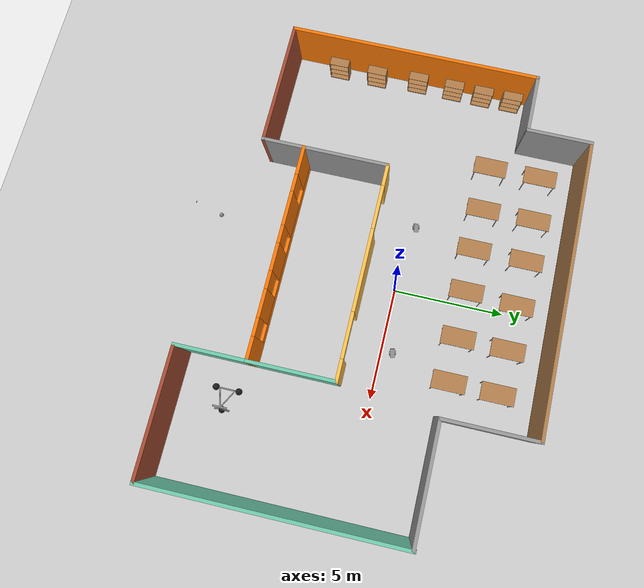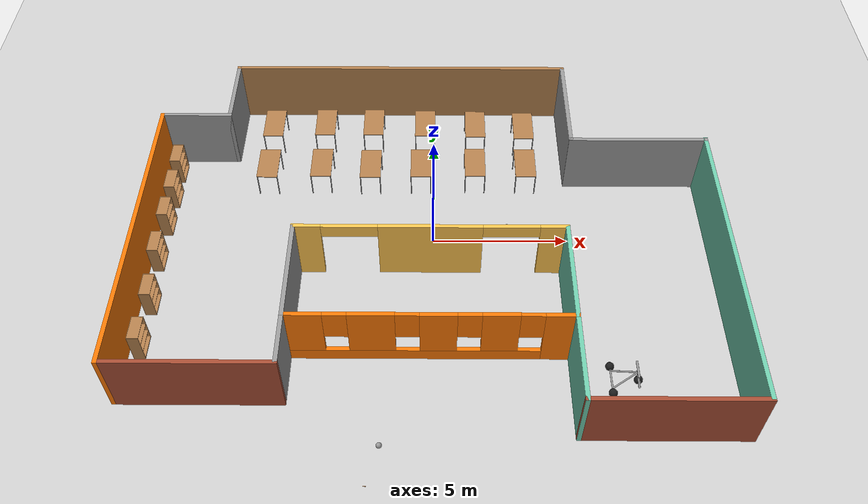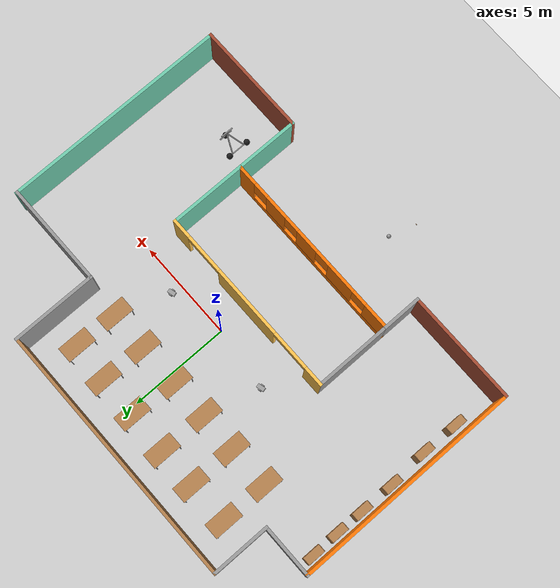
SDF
<sdf version="1.6">
 <world name="default">
  <plugin name="welcome_message" filename="libwelcome_message.so"/>
  <light name="sun" type="directional">
   <pose>0 0 10 0 -0 0</pose>
   <diffuse>0.8 0.8 0.8 1</diffuse>
   <specular>0.2 0.2 0.2 1</specular>
   <attenuation>
    <range>1000</range>
    <constant>0.9</constant>
    <linear>0.01</linear>
    <quadratic>0.001</quadratic>
   </attenuation>
   <direction>-0.5 0.1 -0.9</direction>
  </light>
  <model name="ground_plane">
   <static>1</static>
   <link name="link">
    <collision name="collision">
     <geometry><plane><normal>0 0 1</normal><size>100 100</size></plane></geometry>
     <surface>
      <contact><collide_bitmask>65535</collide_bitmask></contact>
      <friction><ode><mu>100</mu><mu2>50</mu2></ode></friction>
     </surface>
    </collision>
    <visual name="visual">
     <cast_shadows>0</cast_shadows>
     <geometry><plane><normal>0 0 1</normal><size>100 100</size></plane></geometry>
     <material>
      <script><uri>file://media/materials/scripts/gazebo.material</uri><name>Gazebo/Grey</name></script>
     </material>
    </visual>
   </link>
  </model>
  <gravity>0 0 -9.8</gravity>
  <magnetic_field>6e-06 2.3e-05 -4.2e-05</magnetic_field>
  <atmosphere type="adiabatic"/>
  <physics name="default_physics" default="0" type="ode">
   <max_step_size>0.001</max_step_size>
   <real_time_factor>1</real_time_factor>
   <real_time_update_rate>1000</real_time_update_rate>
  </physics>
  <scene><ambient>0.4 0.4 0.4 1</ambient><background>0.7 0.7 0.7 1</background><shadows>1</shadows></scene>
  <audio><device>default</device></audio>
  <spherical_coordinates>
   <surface_model>EARTH_WGS84</surface_model>
   <latitude_deg>0</latitude_deg>
   <longitude_deg>0</longitude_deg>
   <elevation>0</elevation>
   <heading_deg>0</heading_deg>
  </spherical_coordinates>
  <model name="Building">
   <pose>-0.12037 -0.61393 0 0 -0 0</pose>
   <link name="Wall_0">
    <collision name="Wall_0_Collision">
     <geometry><box><size>13.25 0.15 2.5</size></box></geometry>
     <pose>0 0 1.25 0 -0 0</pose>
    </collision>
    <visual name="Wall_0_Visual">
     <pose>0 0 1.25 0 -0 0</pose>
     <geometry><box><size>13.25 0.15 2.5</size></box></geometry>
     <material>
      <script><uri>file://media/materials/scripts/gazebo.material</uri><name>Gazebo/Wood</name></script>
      <ambient>1 1 1 1</ambient>
     </material>
     <meta><layer>0</layer></meta>
    </visual>
    <pose>-1.25 7.725 0 0 -0 0</pose>
   </link>
   <link name="Wall_1">
    <collision name="Wall_1_Collision">
     <geometry><box><size>4.27249 0.15 2.5</size></box></geometry>
     <pose>0 0 1.25 0 -0 0</pose>
    </collision>
    <visual name="Wall_1_Visual">
     <pose>0 0 1.25 0 -0 0</pose>
     <geometry><box><size>4.27249 0.15 2.5</size></box></geometry>
     <material>
      <script><uri>file://media/materials/scripts/gazebo.material</uri><name>Gazebo/Grey</name></script>
      <ambient>1 1 1 1</ambient>
     </material>
     <meta><layer>0</layer></meta>
    </visual>
    <pose>5.3 5.66375 0 0 -0 -1.5708</pose>
   </link>
   <link name="Wall_10">
    <collision name="Wall_10_Collision">
     <geometry><box><size>2.75 0.15 2.5</size></box></geometry>
     <pose>0 0 1.25 0 -0 0</pose>
    </collision>
    <visual name="Wall_10_Visual">
     <pose>0 0 1.25 0 -0 0</pose>
     <geometry><box><size>2.75 0.15 2.5</size></box></geometry>
     <material>
      <script><uri>file://media/materials/scripts/gazebo.material</uri><name>Gazebo/Grey</name></script>
      <ambient>1 1 1 1</ambient>
     </material>
     <meta><layer>0</layer></meta>
    </visual>
    <pose>-9.1 4.875 0 0 -0 0</pose>
   </link>
   <link name="Wall_11">
    <collision name="Wall_11_Collision">
     <geometry><box><size>3 0.15 2.5</size></box></geometry>
     <pose>0 0 1.25 0 -0 0</pose>
    </collision>
    <visual name="Wall_11_Visual">
     <pose>0 0 1.25 0 -0 0</pose>
     <geometry><box><size>3 0.15 2.5</size></box></geometry>
     <material>
      <script><uri>file://media/materials/scripts/gazebo.material</uri><name>Gazebo/Grey</name></script>
      <ambient>1 1 1 1</ambient>
     </material>
     <meta><layer>0</layer></meta>
    </visual>
    <pose>-7.8 6.3 0 0 -0 1.5708</pose>
   </link>
   <link name="Wall_15">
    <collision name="Wall_15_Collision">
     <geometry><box><size>3.89729 0.15 2.5</size></box></geometry>
     <pose>0 0 1.25 0 -0 0</pose>
    </collision>
    <visual name="Wall_15_Visual">
     <pose>0 0 1.25 0 -0 0</pose>
     <geometry><box><size>3.89729 0.15 2.5</size></box></geometry>
     <material>
      <script><uri>file://media/materials/scripts/gazebo.material</uri><name>Gazebo/Grey</name></script>
      <ambient>1 1 1 1</ambient>
     </material>
     <meta><layer>0</layer></meta>
    </visual>
    <pose>-4.8 -2.75136 0 0 -0 1.5708</pose>
   </link>
   <link name="Wall_16">
    <pose>0 -0.837255 0 0 -0 0</pose>
    <visual name="Wall_16_Visual_0">
     <pose>-4.35572 0 1.25 0 -0 0</pose>
     <geometry><box><size>1.03855 0.15 2.5</size></box></geometry>
     <material>
      <script><uri>file://media/materials/scripts/gazebo.material</uri><name>Gazebo/Grey</name></script>
      <ambient>1 0.764706 0.305882 1</ambient>
     </material>
     <meta><layer>0</layer></meta>
    </visual>
    <collision name="Wall_16_Collision_0">
     <geometry><box><size>1.03855 0.15 2.5</size></box></geometry>
     <pose>-4.35572 0 1.25 0 -0 0</pose>
    </collision>
    <visual name="Wall_16_Visual_1">
     <pose>0.006927 0 1.25 0 -0 0</pose>
     <geometry><box><size>3.68675 0.15 2.5</size></box></geometry>
     <material>
      <script><uri>file://media/materials/scripts/gazebo.material</uri><name>Gazebo/Grey</name></script>
      <ambient>1 0.764706 0.305882 1</ambient>
     </material>
     <meta><layer>0</layer></meta>
    </visual>
    <collision name="Wall_16_Collision_1">
     <geometry><box><size>3.68675 0.15 2.5</size></box></geometry>
     <pose>0.006927 0 1.25 0 -0 0</pose>
    </collision>
    <visual name="Wall_16_Visual_2">
     <pose>4.36265 0 1.25 0 -0 0</pose>
     <geometry><box><size>1.0247 0.15 2.5</size></box></geometry>
     <material>
      <script><uri>file://media/materials/scripts/gazebo.material</uri><name>Gazebo/Grey</name></script>
      <ambient>1 0.764706 0.305882 1</ambient>
     </material>
     <meta><layer>0</layer></meta>
    </visual>
    <collision name="Wall_16_Collision_2">
     <geometry><box><size>1.0247 0.15 2.5</size></box></geometry>
     <pose>4.36265 0 1.25 0 -0 0</pose>
    </collision>
    <visual name="Wall_16_Visual_3">
     <pose>-2.83645 0 2.25 0 -0 0</pose>
     <geometry><box><size>2 0.15 0.5</size></box></geometry>
     <material>
      <script><uri>file://media/materials/scripts/gazebo.material</uri><name>Gazebo/Grey</name></script>
      <ambient>1 0.764706 0.305882 1</ambient>
     </material>
     <meta><layer>0</layer></meta>
    </visual>
    <collision name="Wall_16_Collision_3">
     <geometry><box><size>2 0.15 0.5</size></box></geometry>
     <pose>-2.83645 0 2.25 0 -0 0</pose>
    </collision>
    <visual name="Wall_16_Visual_4">
     <pose>2.8503 0 2.25 0 -0 0</pose>
     <geometry><box><size>2 0.15 0.5</size></box></geometry>
     <material>
      <script><uri>file://media/materials/scripts/gazebo.material</uri><name>Gazebo/Grey</name></script>
      <ambient>1 0.764706 0.305882 1</ambient>
     </material>
     <meta><layer>0</layer></meta>
    </visual>
    <collision name="Wall_16_Collision_4">
     <geometry><box><size>2 0.15 0.5</size></box></geometry>
     <pose>2.8503 0 2.25 0 -0 0</pose>
    </collision>
   </link>
   <link name="Wall_17">
    <collision name="Wall_17_Collision">
     <geometry><box><size>3.89729 0.15 2.5</size></box></geometry>
     <pose>0 0 1.25 0 -0 0</pose>
    </collision>
    <visual name="Wall_17_Visual">
     <pose>0 0 1.25 0 -0 0</pose>
     <geometry><box><size>3.89729 0.15 2.5</size></box></geometry>
     <material>
      <script><uri>file://media/materials/scripts/gazebo.material</uri><name>Gazebo/Grey</name></script>
      <ambient>0.435294 0.796078 0.67451 1</ambient>
     </material>
     <meta><layer>0</layer></meta>
    </visual>
    <pose>4.8 -2.75136 0 0 -0 -1.5708</pose>
   </link>
   <link name="Wall_2">
    <collision name="Wall_2_Collision">
     <geometry><box><size>5.25 0.15 2.5</size></box></geometry>
     <pose>0 0 1.25 0 -0 0</pose>
    </collision>
    <visual name="Wall_2_Visual">
     <pose>0 0 1.25 0 -0 0</pose>
     <geometry><box><size>5.25 0.15 2.5</size></box></geometry>
     <material>
      <script><uri>file://media/materials/scripts/gazebo.material</uri><name>Gazebo/Grey</name></script>
      <ambient>1 1 1 1</ambient>
     </material>
     <meta><layer>0</layer></meta>
    </visual>
    <pose>7.85 3.56733 0 0 -0 0</pose>
   </link>
   <link name="Wall_3">
    <collision name="Wall_3_Collision">
     <geometry><box><size>11.4775 0.15 2.5</size></box></geometry>
     <pose>0 0 1.25 0 -0 0</pose>
    </collision>
    <visual name="Wall_3_Visual">
     <pose>0 0 1.25 0 -0 0</pose>
     <geometry><box><size>11.4775 0.15 2.5</size></box></geometry>
     <material>
      <script><uri>file://media/materials/scripts/gazebo.material</uri><name>Gazebo/Grey</name></script>
      <ambient>0.435294 0.796078 0.67451 1</ambient>
     </material>
     <meta><layer>0</layer></meta>
    </visual>
    <pose>10.4 -2.06125 0 0 -0 -1.5708</pose>
   </link>
   <link name="Wall_4">
    <collision name="Wall_4_Collision">
     <geometry><box><size>5.75 0.15 2.5</size></box></geometry>
     <pose>0 0 1.25 0 -0 0</pose>
    </collision>
    <visual name="Wall_4_Visual">
     <pose>0 0 1.25 0 -0 0</pose>
     <geometry><box><size>5.75 0.15 2.5</size></box></geometry>
     <material>
      <script><uri>file://media/materials/scripts/gazebo.material</uri><name>Gazebo/Bricks</name></script>
      <ambient>1 1 1 1</ambient>
     </material>
     <meta><layer>0</layer></meta>
    </visual>
    <pose>7.6 -7.725 0 0 -0 3.14159</pose>
   </link>
   <link name="Wall_5">
    <collision name="Wall_5_Collision">
     <geometry><box><size>3.25 0.15 2.5</size></box></geometry>
     <pose>0 0 1.25 0 -0 0</pose>
    </collision>
    <visual name="Wall_5_Visual">
     <pose>0 0 1.25 0 -0 0</pose>
     <geometry><box><size>3.25 0.15 2.5</size></box></geometry>
     <material>
      <script><uri>file://media/materials/scripts/gazebo.material</uri><name>Gazebo/Grey</name></script>
      <ambient>0.435294 0.796078 0.67451 1</ambient>
     </material>
     <meta><layer>0</layer></meta>
    </visual>
    <pose>4.8 -6.175 0 0 -0 1.5708</pose>
   </link>
   <link name="Wall_6">
    <pose>0 -4.625 0 0 -0 3.14159</pose>
    <visual name="Wall_6_Visual_0">
     <pose>-4.31909 0 1.25 0 -0 0</pose>
     <geometry><box><size>1.11182 0.15 2.5</size></box></geometry>
     <material>
      <script><uri>file://media/materials/scripts/gazebo.material</uri><name>Gazebo/Grey</name></script>
      <ambient>0.996078 0.47451 0.0196078 1</ambient>
     </material>
     <meta><layer>0</layer></meta>
    </visual>
    <collision name="Wall_6_Collision_0">
     <geometry><box><size>1.11182 0.15 2.5</size></box></geometry>
     <pose>-4.31909 0 1.25 0 -0 0</pose>
    </collision>
    <visual name="Wall_6_Visual_1">
     <pose>0.555911 0 0.25 0 -0 0</pose>
     <geometry><box><size>8.63818 0.15 0.5</size></box></geometry>
     <material>
      <script><uri>file://media/materials/scripts/gazebo.material</uri><name>Gazebo/Grey</name></script>
      <ambient>0.996078 0.47451 0.0196078 1</ambient>
     </material>
     <meta><layer>0</layer></meta>
    </visual>
    <collision name="Wall_6_Collision_1">
     <geometry><box><size>8.63818 0.15 0.5</size></box></geometry>
     <pose>0.555911 0 0.25 0 -0 0</pose>
    </collision>
    <visual name="Wall_6_Visual_2">
     <pose>-2.33907 0 1.5 0 -0 0</pose>
     <geometry><box><size>1.24822 0.15 2</size></box></geometry>
     <material>
      <script><uri>file://media/materials/scripts/gazebo.material</uri><name>Gazebo/Grey</name></script>
      <ambient>0.996078 0.47451 0.0196078 1</ambient>
     </material>
     <meta><layer>0</layer></meta>
    </visual>
    <collision name="Wall_6_Collision_2">
     <geometry><box><size>1.24822 0.15 2</size></box></geometry>
     <pose>-2.33907 0 1.5 0 -0 0</pose>
    </collision>
    <visual name="Wall_6_Visual_3">
     <pose>-0.290856 0 1.5 0 -0 0</pose>
     <geometry><box><size>1.24822 0.15 2</size></box></geometry>
     <material>
      <script><uri>file://media/materials/scripts/gazebo.material</uri><name>Gazebo/Grey</name></script>
      <ambient>0.996078 0.47451 0.0196078 1</ambient>
     </material>
     <meta><layer>0</layer></meta>
    </visual>
    <collision name="Wall_6_Collision_3">
     <geometry><box><size>1.24822 0.15 2</size></box></geometry>
     <pose>-0.290856 0 1.5 0 -0 0</pose>
    </collision>
    <visual name="Wall_6_Visual_4">
     <pose>1.91696 0 1.5 0 -0 0</pose>
     <geometry><box><size>1.56742 0.15 2</size></box></geometry>
     <material>
      <script><uri>file://media/materials/scripts/gazebo.material</uri><name>Gazebo/Grey</name></script>
      <ambient>0.996078 0.47451 0.0196078 1</ambient>
     </material>
     <meta><layer>0</layer></meta>
    </visual>
    <collision name="Wall_6_Collision_4">
     <geometry><box><size>1.56742 0.15 2</size></box></geometry>
     <pose>1.91696 0 1.5 0 -0 0</pose>
    </collision>
    <visual name="Wall_6_Visual_5">
     <pose>4.18783 0 1.5 0 -0 0</pose>
     <geometry><box><size>1.37433 0.15 2</size></box></geometry>
     <material>
      <script><uri>file://media/materials/scripts/gazebo.material</uri><name>Gazebo/Grey</name></script>
      <ambient>0.996078 0.47451 0.0196078 1</ambient>
     </material>
     <meta><layer>0</layer></meta>
    </visual>
    <collision name="Wall_6_Collision_5">
     <geometry><box><size>1.37433 0.15 2</size></box></geometry>
     <pose>4.18783 0 1.5 0 -0 0</pose>
    </collision>
    <visual name="Wall_6_Visual_6">
     <pose>-3.36318 0 1.9 0 -0 0</pose>
     <geometry><box><size>0.8 0.15 1.2</size></box></geometry>
     <material>
      <script><uri>file://media/materials/scripts/gazebo.material</uri><name>Gazebo/Grey</name></script>
      <ambient>0.996078 0.47451 0.0196078 1</ambient>
     </material>
     <meta><layer>0</layer></meta>
    </visual>
    <collision name="Wall_6_Collision_6">
     <geometry><box><size>0.8 0.15 1.2</size></box></geometry>
     <pose>-3.36318 0 1.9 0 -0 0</pose>
    </collision>
    <visual name="Wall_6_Visual_7">
     <pose>-1.31496 0 1.9 0 -0 0</pose>
     <geometry><box><size>0.8 0.15 1.2</size></box></geometry>
     <material>
      <script><uri>file://media/materials/scripts/gazebo.material</uri><name>Gazebo/Grey</name></script>
      <ambient>0.996078 0.47451 0.0196078 1</ambient>
     </material>
     <meta><layer>0</layer></meta>
    </visual>
    <collision name="Wall_6_Collision_7">
     <geometry><box><size>0.8 0.15 1.2</size></box></geometry>
     <pose>-1.31496 0 1.9 0 -0 0</pose>
    </collision>
    <visual name="Wall_6_Visual_8">
     <pose>0.733252 0 1.9 0 -0 0</pose>
     <geometry><box><size>0.8 0.15 1.2</size></box></geometry>
     <material>
      <script><uri>file://media/materials/scripts/gazebo.material</uri><name>Gazebo/Grey</name></script>
      <ambient>0.996078 0.47451 0.0196078 1</ambient>
     </material>
     <meta><layer>0</layer></meta>
    </visual>
    <collision name="Wall_6_Collision_8">
     <geometry><box><size>0.8 0.15 1.2</size></box></geometry>
     <pose>0.733252 0 1.9 0 -0 0</pose>
    </collision>
    <visual name="Wall_6_Visual_9">
     <pose>3.10067 0 1.9 0 -0 0</pose>
     <geometry><box><size>0.8 0.15 1.2</size></box></geometry>
     <material>
      <script><uri>file://media/materials/scripts/gazebo.material</uri><name>Gazebo/Grey</name></script>
      <ambient>0.996078 0.47451 0.0196078 1</ambient>
     </material>
     <meta><layer>0</layer></meta>
    </visual>
    <collision name="Wall_6_Collision_9">
     <geometry><box><size>0.8 0.15 1.2</size></box></geometry>
     <pose>3.10067 0 1.9 0 -0 0</pose>
    </collision>
   </link>
   <link name="Wall_7">
    <collision name="Wall_7_Collision">
     <geometry><box><size>2 0.15 2.5</size></box></geometry>
     <pose>0 0 1.25 0 -0 0</pose>
    </collision>
    <visual name="Wall_7_Visual">
     <pose>0 0 1.25 0 -0 0</pose>
     <geometry><box><size>2 0.15 2.5</size></box></geometry>
     <material>
      <script><uri>file://media/materials/scripts/gazebo.material</uri><name>Gazebo/Grey</name></script>
      <ambient>1 1 1 1</ambient>
     </material>
     <meta><layer>0</layer></meta>
    </visual>
    <pose>-4.8 -5.55 0 0 -0 -1.5708</pose>
   </link>
   <link name="Wall_8">
    <collision name="Wall_8_Collision">
     <geometry><box><size>5.75 0.15 2.5</size></box></geometry>
     <pose>0 0 1.25 0 -0 0</pose>
    </collision>
    <visual name="Wall_8_Visual">
     <pose>0 0 1.25 0 -0 0</pose>
     <geometry><box><size>5.75 0.15 2.5</size></box></geometry>
     <material>
      <script><uri>file://media/materials/scripts/gazebo.material</uri><name>Gazebo/Bricks</name></script>
      <ambient>1 1 1 1</ambient>
     </material>
     <meta><layer>0</layer></meta>
    </visual>
    <pose>-7.6 -6.475 0 0 -0 3.14159</pose>
   </link>
   <link name="Wall_9">
    <collision name="Wall_9_Collision">
     <geometry><box><size>11.5 0.15 2.5</size></box></geometry>
     <pose>0 0 1.25 0 -0 0</pose>
    </collision>
    <visual name="Wall_9_Visual">
     <pose>0 0 1.25 0 -0 0</pose>
     <geometry><box><size>11.5 0.15 2.5</size></box></geometry>
     <material>
      <script><uri>file://media/materials/scripts/gazebo.material</uri><name>Gazebo/Grey</name></script>
      <ambient>0.996078 0.47451 0.0196078 1</ambient>
     </material>
     <meta><layer>0</layer></meta>
    </visual>
    <pose>-10.4 -0.8 0 0 -0 1.5708</pose>
   </link>
   <static>1</static>
  </model>
  <model name="bookshelf">
   <static>1</static>
   <link name="link">
    <inertial><mass>1</mass></inertial>
    <collision name="back">
     <pose>0 0.005 0.6 0 -0 0</pose>
     <geometry><box><size>0.9 0.01 1.2</size></box></geometry>
    </collision>
    <visual name="visual1">
     <pose>0 0.005 0.6 0 -0 0</pose>
     <geometry><box><size>0.9 0.01 1.2</size></box></geometry>
     <material>
      <script><uri>file://media/materials/scripts/gazebo.material</uri><name>Gazebo/Wood</name></script>
     </material>
    </visual>
    <collision name="left_side">
     <pose>0.45 -0.195 0.6 0 -0 0</pose>
     <geometry><box><size>0.02 0.4 1.2</size></box></geometry>
    </collision>
    <visual name="visual2">
     <pose>0.45 -0.195 0.6 0 -0 0</pose>
     <geometry><box><size>0.02 0.4 1.2</size></box></geometry>
     <material>
      <script><uri>file://media/materials/scripts/gazebo.material</uri><name>Gazebo/Wood</name></script>
     </material>
    </visual>
    <collision name="right_side">
     <pose>-0.45 -0.195 0.6 0 -0 0</pose>
     <geometry><box><size>0.02 0.4 1.2</size></box></geometry>
    </collision>
    <visual name="visual3">
     <pose>-0.45 -0.195 0.6 0 -0 0</pose>
     <geometry><box><size>0.02 0.4 1.2</size></box></geometry>
     <material>
      <script><uri>file://media/materials/scripts/gazebo.material</uri><name>Gazebo/Wood</name></script>
     </material>
    </visual>
    <collision name="bottom">
     <pose>0 -0.195 0.03 0 -0 0</pose>
     <geometry><box><size>0.88 0.4 0.06</size></box></geometry>
    </collision>
    <visual name="visual4">
     <pose>0 -0.195 0.03 0 -0 0</pose>
     <geometry><box><size>0.88 0.4 0.06</size></box></geometry>
     <material>
      <script><uri>file://media/materials/scripts/gazebo.material</uri><name>Gazebo/Wood</name></script>
     </material>
    </visual>
    <collision name="top">
     <pose>0 -0.195 1.19 0 -0 0</pose>
     <geometry><box><size>0.88 0.4 0.02</size></box></geometry>
    </collision>
    <visual name="visual5">
     <pose>0 -0.195 1.19 0 -0 0</pose>
     <geometry><box><size>0.88 0.4 0.02</size></box></geometry>
     <material>
      <script><uri>file://media/materials/scripts/gazebo.material</uri><name>Gazebo/Wood</name></script>
     </material>
    </visual>
    <collision name="low_shelf">
     <pose>0 -0.195 0.43 0 -0 0</pose>
     <geometry><box><size>0.88 0.4 0.02</size></box></geometry>
    </collision>
    <visual name="visual6">
     <pose>0 -0.195 0.43 0 -0 0</pose>
     <geometry><box><size>0.88 0.4 0.02</size></box></geometry>
     <material>
      <script><uri>file://media/materials/scripts/gazebo.material</uri><name>Gazebo/Wood</name></script>
     </material>
    </visual>
    <collision name="high_shelf">
     <pose>0 -0.195 0.8 0 -0 0</pose>
     <geometry><box><size>0.88 0.4 0.02</size></box></geometry>
    </collision>
    <visual name="visual7">
     <pose>0 -0.195 0.8 0 -0 0</pose>
     <geometry><box><size>0.88 0.4 0.02</size></box></geometry>
     <material>
      <script><uri>file://media/materials/scripts/gazebo.material</uri><name>Gazebo/Wood</name></script>
     </material>
    </visual>
   </link>
   <pose>-10.3049 3.46726 0 0 -0 1.5708</pose>
  </model>
  <model name="table">
   <static>1</static>
   <link name="link">
    <collision name="surface">
     <pose>0 0 1 0 -0 0</pose>
     <geometry><box><size>1.5 0.8 0.03</size></box></geometry>
     <surface><friction><ode><mu>0.6</mu><mu2>0.6</mu2></ode></friction></surface>
    </collision>
    <visual name="visual1">
     <pose>0 0 1 0 -0 0</pose>
     <geometry><box><size>1.5 0.8 0.03</size></box></geometry>
     <material>
      <script><uri>file://media/materials/scripts/gazebo.material</uri><name>Gazebo/Wood</name></script>
     </material>
    </visual>
    <collision name="front_left_leg">
     <pose>0.68 0.38 0.5 0 -0 0</pose>
     <geometry><cylinder><radius>0.02</radius><length>1</length></cylinder></geometry>
    </collision>
    <visual name="front_left_leg">
     <pose>0.68 0.38 0.5 0 -0 0</pose>
     <geometry><cylinder><radius>0.02</radius><length>1</length></cylinder></geometry>
     <material>
      <script><uri>file://media/materials/scripts/gazebo.material</uri><name>Gazebo/Grey</name></script>
     </material>
    </visual>
    <collision name="front_right_leg">
     <pose>0.68 -0.38 0.5 0 -0 0</pose>
     <geometry><cylinder><radius>0.02</radius><length>1</length></cylinder></geometry>
    </collision>
    <visual name="front_right_leg">
     <pose>0.68 -0.38 0.5 0 -0 0</pose>
     <geometry><cylinder><radius>0.02</radius><length>1</length></cylinder></geometry>
     <material>
      <script><uri>file://media/materials/scripts/gazebo.material</uri><name>Gazebo/Grey</name></script>
     </material>
    </visual>
    <collision name="back_right_leg">
     <pose>-0.68 -0.38 0.5 0 -0 0</pose>
     <geometry><cylinder><radius>0.02</radius><length>1</length></cylinder></geometry>
    </collision>
    <visual name="back_right_leg">
     <pose>-0.68 -0.38 0.5 0 -0 0</pose>
     <geometry><cylinder><radius>0.02</radius><length>1</length></cylinder></geometry>
     <material>
      <script><uri>file://media/materials/scripts/gazebo.material</uri><name>Gazebo/Grey</name></script>
     </material>
    </visual>
    <collision name="back_left_leg">
     <pose>-0.68 0.38 0.5 0 -0 0</pose>
     <geometry><cylinder><radius>0.02</radius><length>1</length></cylinder></geometry>
    </collision>
    <visual name="back_left_leg">
     <pose>-0.68 0.38 0.5 0 -0 0</pose>
     <geometry><cylinder><radius>0.02</radius><length>1</length></cylinder></geometry>
     <material>
      <script><uri>file://media/materials/scripts/gazebo.material</uri><name>Gazebo/Grey</name></script>
     </material>
    </visual>
   </link>
   <pose>-6.47493 5.4138 0 0 -0 1.5708</pose>
  </model>
  <model name="wood_block_10_2_1cm">
   <link name="link">
    <pose>0 0 0.005 0 -0 0</pose>
    <inertial>
     <mass>0.0125</mass>
     <inertia>
      <ixx>7.55208e-07</ixx>
      <ixy>0</ixy>
      <ixz>0</ixz>
      <iyy>1.05208e-05</iyy>
      <iyz>0</iyz>
      <izz>1.10677e-05</izz>
     </inertia>
    </inertial>
    <collision name="collision">
     <geometry><box><size>0.1 0.025 0.01</size></box></geometry>
     <surface>
      <contact>
       <poissons_ratio>0.347</poissons_ratio>
       <elastic_modulus>8.8e+09</elastic_modulus>
       <ode><kp>100000</kp><kd>1</kd><max_vel>1</max_vel><min_depth>0.001</min_depth></ode>
      </contact>
      <friction>
       <torsional>
        <coefficient>1</coefficient>
        <use_patch_radius>0</use_patch_radius>
        <surface_radius>0.05</surface_radius>
       </torsional>
      </friction>
     </surface>
    </collision>
    <visual name="visual">
     <geometry><box><size>0.1 0.025 0.01</size></box></geometry>
     <material>
      <script><uri>file://media/materials/scripts/gazebo.material</uri><name>Gazebo/Wood</name></script>
     </material>
    </visual>
   </link>
   <pose>-2.12101 -10.0279 -0.001 0 -0 0</pose>
  </model>
  <model name="trisphere_cycle">
   <link name="frame">
    <pose>-0.408559 0 0.385023 0 -0.522021 0</pose>
    <inertial>
     <mass>10</mass>
     <inertia><ixx>0.228</ixx><iyy>0.743521</iyy><izz>0.965521</izz><ixy>0</ixy><ixz>0</ixz><iyz>0</iyz></inertia>
    </inertial>
    <collision name="axle_collision">
     <pose>-0.471335 0 0 1.5708 -0 0</pose>
     <geometry><cylinder><length>1.03923</length><radius>0.03</radius></cylinder></geometry>
    </collision>
    <visual name="axle_visual">
     <pose>-0.471335 0 0 1.5708 -0 0</pose>
     <geometry><cylinder><length>1.03923</length><radius>0.03</radius></cylinder></geometry>
     <material>
      <script><uri>file://media/materials/scripts/gazebo.material</uri><name>Gazebo/Grey</name></script>
     </material>
    </visual>
    <collision name="frame_left_collision">
     <pose>0 0.171552 0 -2.79253 1.57079 3.14159</pose>
     <geometry><cylinder><length>1.00317</length><radius>0.03</radius></cylinder></geometry>
    </collision>
    <visual name="frame_left_visual">
     <pose>0 0.171552 0 -2.79253 1.57079 3.14159</pose>
     <geometry><cylinder><length>1.00317</length><radius>0.03</radius></cylinder></geometry>
     <material>
      <script><uri>file://media/materials/scripts/gazebo.material</uri><name>Gazebo/Grey</name></script>
     </material>
    </visual>
    <collision name="frame_right_collision">
     <pose>0 -0.171552 0 2.79253 1.57079 -3.14159</pose>
     <geometry><cylinder><length>1.00317</length><radius>0.03</radius></cylinder></geometry>
    </collision>
    <visual name="frame_right_visual">
     <pose>0 -0.171552 0 2.79253 1.57079 -3.14159</pose>
     <geometry><cylinder><length>1.00317</length><radius>0.03</radius></cylinder></geometry>
     <material>
      <script><uri>file://media/materials/scripts/gazebo.material</uri><name>Gazebo/Grey</name></script>
     </material>
    </visual>
   </link>
   <link name="fork">
    <pose>0.041441 0 0.385023 0 -0.174533 0</pose>
    <inertial>
     <mass>3</mass>
     <inertia>
      <ixx>0.158203</ixx>
      <iyy>0.0583594</iyy>
      <izz>0.102656</izz>
      <ixy>0</ixy>
      <ixz>0</ixz>
      <iyz>0</iyz>
     </inertia>
    </inertial>
    <collision name="handlebars_collision">
     <pose>0 0 0.397748 1.5708 -0 0</pose>
     <geometry><cylinder><length>0.636396</length><radius>0.0375</radius></cylinder></geometry>
    </collision>
    <visual name="handlebars_visual">
     <pose>0 0 0.397748 1.5708 -0 0</pose>
     <geometry><cylinder><length>0.636396</length><radius>0.0375</radius></cylinder></geometry>
     <material>
      <script><uri>file://media/materials/scripts/gazebo.material</uri><name>Gazebo/Grey</name></script>
     </material>
    </visual>
    <collision name="headtube_collision">
     <pose>0 0 0.238649 0 -0 0</pose>
     <geometry><cylinder><length>0.318198</length><radius>0.0375</radius></cylinder></geometry>
    </collision>
    <visual name="headtube_visual">
     <pose>0 0 0.238649 0 -0 0</pose>
     <geometry><cylinder><length>0.318198</length><radius>0.0375</radius></cylinder></geometry>
     <material>
      <script><uri>file://media/materials/scripts/gazebo.material</uri><name>Gazebo/Grey</name></script>
     </material>
    </visual>
    <collision name="spindle_collision">
     <pose>0 0 -0.238649 1.5708 -0 0</pose>
     <geometry><cylinder><length>0.636396</length><radius>0.015</radius></cylinder></geometry>
    </collision>
    <visual name="spindle_visual">
     <pose>0 0 -0.238649 1.5708 -0 0</pose>
     <geometry><cylinder><length>0.636396</length><radius>0.015</radius></cylinder></geometry>
     <material>
      <script><uri>file://media/materials/scripts/gazebo.material</uri><name>Gazebo/Grey</name></script>
     </material>
    </visual>
    <collision name="fork_left_collision">
     <pose>0 0.159099 -0.07955 0.785398 -0 0</pose>
     <geometry><cylinder><length>0.45</length><radius>0.0375</radius></cylinder></geometry>
    </collision>
    <visual name="fork_left_visual">
     <pose>0 0.159099 -0.07955 0.785398 -0 0</pose>
     <geometry><cylinder><length>0.45</length><radius>0.0375</radius></cylinder></geometry>
     <material>
      <script><uri>file://media/materials/scripts/gazebo.material</uri><name>Gazebo/Grey</name></script>
     </material>
    </visual>
    <collision name="fork_right_collision">
     <pose>0 -0.159099 -0.07955 -0.785398 0 0</pose>
     <geometry><cylinder><length>0.45</length><radius>0.0375</radius></cylinder></geometry>
    </collision>
    <visual name="fork_right_visual">
     <pose>0 -0.159099 -0.07955 -0.785398 0 0</pose>
     <geometry><cylinder><length>0.45</length><radius>0.0375</radius></cylinder></geometry>
     <material>
      <script><uri>file://media/materials/scripts/gazebo.material</uri><name>Gazebo/Grey</name></script>
     </material>
    </visual>
   </link>
   <link name="wheel_front">
    <pose>0.082882 0 0.15 0 -0 0</pose>
    <inertial>
     <mass>0.5</mass>
     <inertia><ixx>0.0045</ixx><iyy>0.0045</iyy><izz>0.0045</izz><ixy>0</ixy><ixz>0</ixz><iyz>0</iyz></inertia>
    </inertial>
    <collision name="collision">
     <geometry><sphere><radius>0.15</radius></sphere></geometry>
     <surface><contact><ode><kp>1e+08</kp><kd>1</kd><min_depth>0.0005</min_depth></ode></contact></surface>
    </collision>
    <visual name="visual">
     <geometry><sphere><radius>0.15</radius></sphere></geometry>
     <material>
      <script><uri>file://media/materials/scripts/gazebo.material</uri><name>Gazebo/Black</name></script>
     </material>
    </visual>
   </link>
   <joint name="wheel_front_steer" type="revolute">
    <parent>frame</parent>
    <child>fork</child>
    <axis>
     <xyz>0 0 1</xyz>
     <limit><lower>-0.959931</lower><upper>0.959931</upper></limit>
     <use_parent_model_frame>0</use_parent_model_frame>
     <dynamics><spring_reference>0</spring_reference><spring_stiffness>0</spring_stiffness></dynamics>
    </axis>
   </joint>
   <joint name="wheel_front_spin" type="revolute">
    <parent>fork</parent>
    <child>wheel_front</child>
    <axis>
     <xyz>0 1 0</xyz>
     <use_parent_model_frame>0</use_parent_model_frame>
     <limit><lower>-1e+16</lower><upper>1e+16</upper></limit>
     <dynamics><spring_reference>0</spring_reference><spring_stiffness>0</spring_stiffness></dynamics>
    </axis>
   </joint>
   <link name="wheel_rear_left">
    <pose>-0.817118 0.519615 0.15 0 -0 0</pose>
    <inertial>
     <mass>0.5</mass>
     <inertia><ixx>0.0045</ixx><iyy>0.0045</iyy><izz>0.0045</izz><ixy>0</ixy><ixz>0</ixz><iyz>0</iyz></inertia>
    </inertial>
    <collision name="collision">
     <geometry><sphere><radius>0.15</radius></sphere></geometry>
     <surface><contact><ode><kp>1e+08</kp><kd>1</kd><min_depth>0.0005</min_depth></ode></contact></surface>
    </collision>
    <visual name="visual">
     <geometry><sphere><radius>0.15</radius></sphere></geometry>
     <material>
      <script><uri>file://media/materials/scripts/gazebo.material</uri><name>Gazebo/Black</name></script>
     </material>
    </visual>
   </link>
   <joint name="wheel_rear_left_spin" type="revolute">
    <parent>frame</parent>
    <child>wheel_rear_left</child>
    <axis>
     <xyz>0 1 0</xyz>
     <use_parent_model_frame>0</use_parent_model_frame>
     <limit><lower>-1e+16</lower><upper>1e+16</upper></limit>
     <dynamics><spring_reference>0</spring_reference><spring_stiffness>0</spring_stiffness></dynamics>
    </axis>
   </joint>
   <link name="wheel_rear_right">
    <pose>-0.817118 -0.519615 0.15 0 -0 0</pose>
    <inertial>
     <mass>0.5</mass>
     <inertia><ixx>0.0045</ixx><iyy>0.0045</iyy><izz>0.0045</izz><ixy>0</ixy><ixz>0</ixz><iyz>0</iyz></inertia>
    </inertial>
    <collision name="collision">
     <geometry><sphere><radius>0.15</radius></sphere></geometry>
     <surface><contact><ode><kp>1e+08</kp><kd>1</kd><min_depth>0.0005</min_depth></ode></contact></surface>
    </collision>
    <visual name="visual">
     <geometry><sphere><radius>0.15</radius></sphere></geometry>
     <material>
      <script><uri>file://media/materials/scripts/gazebo.material</uri><name>Gazebo/Black</name></script>
     </material>
    </visual>
   </link>
   <joint name="wheel_rear_right_spin" type="revolute">
    <parent>frame</parent>
    <child>wheel_rear_right</child>
    <axis>
     <xyz>0 1 0</xyz>
     <use_parent_model_frame>0</use_parent_model_frame>
     <limit><lower>-1e+16</lower><upper>1e+16</upper></limit>
     <dynamics><spring_reference>0</spring_reference><spring_stiffness>0</spring_stiffness></dynamics>
    </axis>
   </joint>
   <pose>6.79048 -6.20647 -0.000501 -0 1e-06 -0.000787</pose>
  </model>
  <model name="table_clone">
   <static>1</static>
   <link name="link">
    <collision name="surface">
     <pose>0 0 1 0 -0 0</pose>
     <geometry><box><size>1.5 0.8 0.03</size></box></geometry>
     <surface><friction><ode><mu>0.6</mu><mu2>0.6</mu2></ode></friction></surface>
    </collision>
    <visual name="visual1">
     <pose>0 0 1 0 -0 0</pose>
     <geometry><box><size>1.5 0.8 0.03</size></box></geometry>
     <material>
      <script><uri>file://media/materials/scripts/gazebo.material</uri><name>Gazebo/Wood</name></script>
     </material>
    </visual>
    <collision name="front_left_leg">
     <pose>0.68 0.38 0.5 0 -0 0</pose>
     <geometry><cylinder><radius>0.02</radius><length>1</length></cylinder></geometry>
    </collision>
    <visual name="front_left_leg">
     <pose>0.68 0.38 0.5 0 -0 0</pose>
     <geometry><cylinder><radius>0.02</radius><length>1</length></cylinder></geometry>
     <material>
      <script><uri>file://media/materials/scripts/gazebo.material</uri><name>Gazebo/Grey</name></script>
     </material>
    </visual>
    <collision name="front_right_leg">
     <pose>0.68 -0.38 0.5 0 -0 0</pose>
     <geometry><cylinder><radius>0.02</radius><length>1</length></cylinder></geometry>
    </collision>
    <visual name="front_right_leg">
     <pose>0.68 -0.38 0.5 0 -0 0</pose>
     <geometry><cylinder><radius>0.02</radius><length>1</length></cylinder></geometry>
     <material>
      <script><uri>file://media/materials/scripts/gazebo.material</uri><name>Gazebo/Grey</name></script>
     </material>
    </visual>
    <collision name="back_right_leg">
     <pose>-0.68 -0.38 0.5 0 -0 0</pose>
     <geometry><cylinder><radius>0.02</radius><length>1</length></cylinder></geometry>
    </collision>
    <visual name="back_right_leg">
     <pose>-0.68 -0.38 0.5 0 -0 0</pose>
     <geometry><cylinder><radius>0.02</radius><length>1</length></cylinder></geometry>
     <material>
      <script><uri>file://media/materials/scripts/gazebo.material</uri><name>Gazebo/Grey</name></script>
     </material>
    </visual>
    <collision name="back_left_leg">
     <pose>-0.68 0.38 0.5 0 -0 0</pose>
     <geometry><cylinder><radius>0.02</radius><length>1</length></cylinder></geometry>
    </collision>
    <visual name="back_left_leg">
     <pose>-0.68 0.38 0.5 0 -0 0</pose>
     <geometry><cylinder><radius>0.02</radius><length>1</length></cylinder></geometry>
     <material>
      <script><uri>file://media/materials/scripts/gazebo.material</uri><name>Gazebo/Grey</name></script>
     </material>
    </visual>
   </link>
   <pose>-4.38863 5.46598 0 0 -0 1.5708</pose>
  </model>
  <model name="table_clone_0">
   <static>1</static>
   <link name="link">
    <collision name="surface">
     <pose>0 0 1 0 -0 0</pose>
     <geometry><box><size>1.5 0.8 0.03</size></box></geometry>
     <surface><friction><ode><mu>0.6</mu><mu2>0.6</mu2></ode></friction></surface>
    </collision>
    <visual name="visual1">
     <pose>0 0 1 0 -0 0</pose>
     <geometry><box><size>1.5 0.8 0.03</size></box></geometry>
     <material>
      <script><uri>file://media/materials/scripts/gazebo.material</uri><name>Gazebo/Wood</name></script>
     </material>
    </visual>
    <collision name="front_left_leg">
     <pose>0.68 0.38 0.5 0 -0 0</pose>
     <geometry><cylinder><radius>0.02</radius><length>1</length></cylinder></geometry>
    </collision>
    <visual name="front_left_leg">
     <pose>0.68 0.38 0.5 0 -0 0</pose>
     <geometry><cylinder><radius>0.02</radius><length>1</length></cylinder></geometry>
     <material>
      <script><uri>file://media/materials/scripts/gazebo.material</uri><name>Gazebo/Grey</name></script>
     </material>
    </visual>
    <collision name="front_right_leg">
     <pose>0.68 -0.38 0.5 0 -0 0</pose>
     <geometry><cylinder><radius>0.02</radius><length>1</length></cylinder></geometry>
    </collision>
    <visual name="front_right_leg">
     <pose>0.68 -0.38 0.5 0 -0 0</pose>
     <geometry><cylinder><radius>0.02</radius><length>1</length></cylinder></geometry>
     <material>
      <script><uri>file://media/materials/scripts/gazebo.material</uri><name>Gazebo/Grey</name></script>
     </material>
    </visual>
    <collision name="back_right_leg">
     <pose>-0.68 -0.38 0.5 0 -0 0</pose>
     <geometry><cylinder><radius>0.02</radius><length>1</length></cylinder></geometry>
    </collision>
    <visual name="back_right_leg">
     <pose>-0.68 -0.38 0.5 0 -0 0</pose>
     <geometry><cylinder><radius>0.02</radius><length>1</length></cylinder></geometry>
     <material>
      <script><uri>file://media/materials/scripts/gazebo.material</uri><name>Gazebo/Grey</name></script>
     </material>
    </visual>
    <collision name="back_left_leg">
     <pose>-0.68 0.38 0.5 0 -0 0</pose>
     <geometry><cylinder><radius>0.02</radius><length>1</length></cylinder></geometry>
    </collision>
    <visual name="back_left_leg">
     <pose>-0.68 0.38 0.5 0 -0 0</pose>
     <geometry><cylinder><radius>0.02</radius><length>1</length></cylinder></geometry>
     <material>
      <script><uri>file://media/materials/scripts/gazebo.material</uri><name>Gazebo/Grey</name></script>
     </material>
    </visual>
   </link>
   <pose>-2.44462 5.48292 0 0 -0 1.5708</pose>
  </model>
  <model name="table_clone_1">
   <static>1</static>
   <link name="link">
    <collision name="surface">
     <pose>0 0 1 0 -0 0</pose>
     <geometry><box><size>1.5 0.8 0.03</size></box></geometry>
     <surface><friction><ode><mu>0.6</mu><mu2>0.6</mu2></ode></friction></surface>
    </collision>
    <visual name="visual1">
     <pose>0 0 1 0 -0 0</pose>
     <geometry><box><size>1.5 0.8 0.03</size></box></geometry>
     <material>
      <script><uri>file://media/materials/scripts/gazebo.material</uri><name>Gazebo/Wood</name></script>
     </material>
    </visual>
    <collision name="front_left_leg">
     <pose>0.68 0.38 0.5 0 -0 0</pose>
     <geometry><cylinder><radius>0.02</radius><length>1</length></cylinder></geometry>
    </collision>
    <visual name="front_left_leg">
     <pose>0.68 0.38 0.5 0 -0 0</pose>
     <geometry><cylinder><radius>0.02</radius><length>1</length></cylinder></geometry>
     <material>
      <script><uri>file://media/materials/scripts/gazebo.material</uri><name>Gazebo/Grey</name></script>
     </material>
    </visual>
    <collision name="front_right_leg">
     <pose>0.68 -0.38 0.5 0 -0 0</pose>
     <geometry><cylinder><radius>0.02</radius><length>1</length></cylinder></geometry>
    </collision>
    <visual name="front_right_leg">
     <pose>0.68 -0.38 0.5 0 -0 0</pose>
     <geometry><cylinder><radius>0.02</radius><length>1</length></cylinder></geometry>
     <material>
      <script><uri>file://media/materials/scripts/gazebo.material</uri><name>Gazebo/Grey</name></script>
     </material>
    </visual>
    <collision name="back_right_leg">
     <pose>-0.68 -0.38 0.5 0 -0 0</pose>
     <geometry><cylinder><radius>0.02</radius><length>1</length></cylinder></geometry>
    </collision>
    <visual name="back_right_leg">
     <pose>-0.68 -0.38 0.5 0 -0 0</pose>
     <geometry><cylinder><radius>0.02</radius><length>1</length></cylinder></geometry>
     <material>
      <script><uri>file://media/materials/scripts/gazebo.material</uri><name>Gazebo/Grey</name></script>
     </material>
    </visual>
    <collision name="back_left_leg">
     <pose>-0.68 0.38 0.5 0 -0 0</pose>
     <geometry><cylinder><radius>0.02</radius><length>1</length></cylinder></geometry>
    </collision>
    <visual name="back_left_leg">
     <pose>-0.68 0.38 0.5 0 -0 0</pose>
     <geometry><cylinder><radius>0.02</radius><length>1</length></cylinder></geometry>
     <material>
      <script><uri>file://media/materials/scripts/gazebo.material</uri><name>Gazebo/Grey</name></script>
     </material>
    </visual>
   </link>
   <pose>-0.362196 5.42426 0 0 -0 1.5708</pose>
  </model>
  <model name="table_clone_2">
   <static>1</static>
   <link name="link">
    <collision name="surface">
     <pose>0 0 1 0 -0 0</pose>
     <geometry><box><size>1.5 0.8 0.03</size></box></geometry>
     <surface><friction><ode><mu>0.6</mu><mu2>0.6</mu2></ode></friction></surface>
    </collision>
    <visual name="visual1">
     <pose>0 0 1 0 -0 0</pose>
     <geometry><box><size>1.5 0.8 0.03</size></box></geometry>
     <material>
      <script><uri>file://media/materials/scripts/gazebo.material</uri><name>Gazebo/Wood</name></script>
     </material>
    </visual>
    <collision name="front_left_leg">
     <pose>0.68 0.38 0.5 0 -0 0</pose>
     <geometry><cylinder><radius>0.02</radius><length>1</length></cylinder></geometry>
    </collision>
    <visual name="front_left_leg">
     <pose>0.68 0.38 0.5 0 -0 0</pose>
     <geometry><cylinder><radius>0.02</radius><length>1</length></cylinder></geometry>
     <material>
      <script><uri>file://media/materials/scripts/gazebo.material</uri><name>Gazebo/Grey</name></script>
     </material>
    </visual>
    <collision name="front_right_leg">
     <pose>0.68 -0.38 0.5 0 -0 0</pose>
     <geometry><cylinder><radius>0.02</radius><length>1</length></cylinder></geometry>
    </collision>
    <visual name="front_right_leg">
     <pose>0.68 -0.38 0.5 0 -0 0</pose>
     <geometry><cylinder><radius>0.02</radius><length>1</length></cylinder></geometry>
     <material>
      <script><uri>file://media/materials/scripts/gazebo.material</uri><name>Gazebo/Grey</name></script>
     </material>
    </visual>
    <collision name="back_right_leg">
     <pose>-0.68 -0.38 0.5 0 -0 0</pose>
     <geometry><cylinder><radius>0.02</radius><length>1</length></cylinder></geometry>
    </collision>
    <visual name="back_right_leg">
     <pose>-0.68 -0.38 0.5 0 -0 0</pose>
     <geometry><cylinder><radius>0.02</radius><length>1</length></cylinder></geometry>
     <material>
      <script><uri>file://media/materials/scripts/gazebo.material</uri><name>Gazebo/Grey</name></script>
     </material>
    </visual>
    <collision name="back_left_leg">
     <pose>-0.68 0.38 0.5 0 -0 0</pose>
     <geometry><cylinder><radius>0.02</radius><length>1</length></cylinder></geometry>
    </collision>
    <visual name="back_left_leg">
     <pose>-0.68 0.38 0.5 0 -0 0</pose>
     <geometry><cylinder><radius>0.02</radius><length>1</length></cylinder></geometry>
     <material>
      <script><uri>file://media/materials/scripts/gazebo.material</uri><name>Gazebo/Grey</name></script>
     </material>
    </visual>
   </link>
   <pose>1.6624 5.38113 0 0 -0 1.5708</pose>
  </model>
  <model name="table_clone_3">
   <static>1</static>
   <link name="link">
    <collision name="surface">
     <pose>0 0 1 0 -0 0</pose>
     <geometry><box><size>1.5 0.8 0.03</size></box></geometry>
     <surface><friction><ode><mu>0.6</mu><mu2>0.6</mu2></ode></friction></surface>
    </collision>
    <visual name="visual1">
     <pose>0 0 1 0 -0 0</pose>
     <geometry><box><size>1.5 0.8 0.03</size></box></geometry>
     <material>
      <script><uri>file://media/materials/scripts/gazebo.material</uri><name>Gazebo/Wood</name></script>
     </material>
    </visual>
    <collision name="front_left_leg">
     <pose>0.68 0.38 0.5 0 -0 0</pose>
     <geometry><cylinder><radius>0.02</radius><length>1</length></cylinder></geometry>
    </collision>
    <visual name="front_left_leg">
     <pose>0.68 0.38 0.5 0 -0 0</pose>
     <geometry><cylinder><radius>0.02</radius><length>1</length></cylinder></geometry>
     <material>
      <script><uri>file://media/materials/scripts/gazebo.material</uri><name>Gazebo/Grey</name></script>
     </material>
    </visual>
    <collision name="front_right_leg">
     <pose>0.68 -0.38 0.5 0 -0 0</pose>
     <geometry><cylinder><radius>0.02</radius><length>1</length></cylinder></geometry>
    </collision>
    <visual name="front_right_leg">
     <pose>0.68 -0.38 0.5 0 -0 0</pose>
     <geometry><cylinder><radius>0.02</radius><length>1</length></cylinder></geometry>
     <material>
      <script><uri>file://media/materials/scripts/gazebo.material</uri><name>Gazebo/Grey</name></script>
     </material>
    </visual>
    <collision name="back_right_leg">
     <pose>-0.68 -0.38 0.5 0 -0 0</pose>
     <geometry><cylinder><radius>0.02</radius><length>1</length></cylinder></geometry>
    </collision>
    <visual name="back_right_leg">
     <pose>-0.68 -0.38 0.5 0 -0 0</pose>
     <geometry><cylinder><radius>0.02</radius><length>1</length></cylinder></geometry>
     <material>
      <script><uri>file://media/materials/scripts/gazebo.material</uri><name>Gazebo/Grey</name></script>
     </material>
    </visual>
    <collision name="back_left_leg">
     <pose>-0.68 0.38 0.5 0 -0 0</pose>
     <geometry><cylinder><radius>0.02</radius><length>1</length></cylinder></geometry>
    </collision>
    <visual name="back_left_leg">
     <pose>-0.68 0.38 0.5 0 -0 0</pose>
     <geometry><cylinder><radius>0.02</radius><length>1</length></cylinder></geometry>
     <material>
      <script><uri>file://media/materials/scripts/gazebo.material</uri><name>Gazebo/Grey</name></script>
     </material>
    </visual>
   </link>
   <pose>3.59959 5.29445 0 0 -0 1.5708</pose>
  </model>
  <model name="table_clone_4">
   <static>1</static>
   <link name="link">
    <collision name="surface">
     <pose>0 0 1 0 -0 0</pose>
     <geometry><box><size>1.5 0.8 0.03</size></box></geometry>
     <surface><friction><ode><mu>0.6</mu><mu2>0.6</mu2></ode></friction></surface>
    </collision>
    <visual name="visual1">
     <pose>0 0 1 0 -0 0</pose>
     <geometry><box><size>1.5 0.8 0.03</size></box></geometry>
     <material>
      <script><uri>file://media/materials/scripts/gazebo.material</uri><name>Gazebo/Wood</name></script>
     </material>
    </visual>
    <collision name="front_left_leg">
     <pose>0.68 0.38 0.5 0 -0 0</pose>
     <geometry><cylinder><radius>0.02</radius><length>1</length></cylinder></geometry>
    </collision>
    <visual name="front_left_leg">
     <pose>0.68 0.38 0.5 0 -0 0</pose>
     <geometry><cylinder><radius>0.02</radius><length>1</length></cylinder></geometry>
     <material>
      <script><uri>file://media/materials/scripts/gazebo.material</uri><name>Gazebo/Grey</name></script>
     </material>
    </visual>
    <collision name="front_right_leg">
     <pose>0.68 -0.38 0.5 0 -0 0</pose>
     <geometry><cylinder><radius>0.02</radius><length>1</length></cylinder></geometry>
    </collision>
    <visual name="front_right_leg">
     <pose>0.68 -0.38 0.5 0 -0 0</pose>
     <geometry><cylinder><radius>0.02</radius><length>1</length></cylinder></geometry>
     <material>
      <script><uri>file://media/materials/scripts/gazebo.material</uri><name>Gazebo/Grey</name></script>
     </material>
    </visual>
    <collision name="back_right_leg">
     <pose>-0.68 -0.38 0.5 0 -0 0</pose>
     <geometry><cylinder><radius>0.02</radius><length>1</length></cylinder></geometry>
    </collision>
    <visual name="back_right_leg">
     <pose>-0.68 -0.38 0.5 0 -0 0</pose>
     <geometry><cylinder><radius>0.02</radius><length>1</length></cylinder></geometry>
     <material>
      <script><uri>file://media/materials/scripts/gazebo.material</uri><name>Gazebo/Grey</name></script>
     </material>
    </visual>
    <collision name="back_left_leg">
     <pose>-0.68 0.38 0.5 0 -0 0</pose>
     <geometry><cylinder><radius>0.02</radius><length>1</length></cylinder></geometry>
    </collision>
    <visual name="back_left_leg">
     <pose>-0.68 0.38 0.5 0 -0 0</pose>
     <geometry><cylinder><radius>0.02</radius><length>1</length></cylinder></geometry>
     <material>
      <script><uri>file://media/materials/scripts/gazebo.material</uri><name>Gazebo/Grey</name></script>
     </material>
    </visual>
   </link>
   <pose>3.5646 3.15771 0 0 -0 1.5708</pose>
  </model>
  <model name="table_clone_5">
   <static>1</static>
   <link name="link">
    <collision name="surface">
     <pose>0 0 1 0 -0 0</pose>
     <geometry><box><size>1.5 0.8 0.03</size></box></geometry>
     <surface><friction><ode><mu>0.6</mu><mu2>0.6</mu2></ode></friction></surface>
    </collision>
    <visual name="visual1">
     <pose>0 0 1 0 -0 0</pose>
     <geometry><box><size>1.5 0.8 0.03</size></box></geometry>
     <material>
      <script><uri>file://media/materials/scripts/gazebo.material</uri><name>Gazebo/Wood</name></script>
     </material>
    </visual>
    <collision name="front_left_leg">
     <pose>0.68 0.38 0.5 0 -0 0</pose>
     <geometry><cylinder><radius>0.02</radius><length>1</length></cylinder></geometry>
    </collision>
    <visual name="front_left_leg">
     <pose>0.68 0.38 0.5 0 -0 0</pose>
     <geometry><cylinder><radius>0.02</radius><length>1</length></cylinder></geometry>
     <material>
      <script><uri>file://media/materials/scripts/gazebo.material</uri><name>Gazebo/Grey</name></script>
     </material>
    </visual>
    <collision name="front_right_leg">
     <pose>0.68 -0.38 0.5 0 -0 0</pose>
     <geometry><cylinder><radius>0.02</radius><length>1</length></cylinder></geometry>
    </collision>
    <visual name="front_right_leg">
     <pose>0.68 -0.38 0.5 0 -0 0</pose>
     <geometry><cylinder><radius>0.02</radius><length>1</length></cylinder></geometry>
     <material>
      <script><uri>file://media/materials/scripts/gazebo.material</uri><name>Gazebo/Grey</name></script>
     </material>
    </visual>
    <collision name="back_right_leg">
     <pose>-0.68 -0.38 0.5 0 -0 0</pose>
     <geometry><cylinder><radius>0.02</radius><length>1</length></cylinder></geometry>
    </collision>
    <visual name="back_right_leg">
     <pose>-0.68 -0.38 0.5 0 -0 0</pose>
     <geometry><cylinder><radius>0.02</radius><length>1</length></cylinder></geometry>
     <material>
      <script><uri>file://media/materials/scripts/gazebo.material</uri><name>Gazebo/Grey</name></script>
     </material>
    </visual>
    <collision name="back_left_leg">
     <pose>-0.68 0.38 0.5 0 -0 0</pose>
     <geometry><cylinder><radius>0.02</radius><length>1</length></cylinder></geometry>
    </collision>
    <visual name="back_left_leg">
     <pose>-0.68 0.38 0.5 0 -0 0</pose>
     <geometry><cylinder><radius>0.02</radius><length>1</length></cylinder></geometry>
     <material>
      <script><uri>file://media/materials/scripts/gazebo.material</uri><name>Gazebo/Grey</name></script>
     </material>
    </visual>
   </link>
   <pose>1.60472 3.17671 0 0 -0 1.5708</pose>
  </model>
  <model name="table_clone_6">
   <static>1</static>
   <link name="link">
    <collision name="surface">
     <pose>0 0 1 0 -0 0</pose>
     <geometry><box><size>1.5 0.8 0.03</size></box></geometry>
     <surface><friction><ode><mu>0.6</mu><mu2>0.6</mu2></ode></friction></surface>
    </collision>
    <visual name="visual1">
     <pose>0 0 1 0 -0 0</pose>
     <geometry><box><size>1.5 0.8 0.03</size></box></geometry>
     <material>
      <script><uri>file://media/materials/scripts/gazebo.material</uri><name>Gazebo/Wood</name></script>
     </material>
    </visual>
    <collision name="front_left_leg">
     <pose>0.68 0.38 0.5 0 -0 0</pose>
     <geometry><cylinder><radius>0.02</radius><length>1</length></cylinder></geometry>
    </collision>
    <visual name="front_left_leg">
     <pose>0.68 0.38 0.5 0 -0 0</pose>
     <geometry><cylinder><radius>0.02</radius><length>1</length></cylinder></geometry>
     <material>
      <script><uri>file://media/materials/scripts/gazebo.material</uri><name>Gazebo/Grey</name></script>
     </material>
    </visual>
    <collision name="front_right_leg">
     <pose>0.68 -0.38 0.5 0 -0 0</pose>
     <geometry><cylinder><radius>0.02</radius><length>1</length></cylinder></geometry>
    </collision>
    <visual name="front_right_leg">
     <pose>0.68 -0.38 0.5 0 -0 0</pose>
     <geometry><cylinder><radius>0.02</radius><length>1</length></cylinder></geometry>
     <material>
      <script><uri>file://media/materials/scripts/gazebo.material</uri><name>Gazebo/Grey</name></script>
     </material>
    </visual>
    <collision name="back_right_leg">
     <pose>-0.68 -0.38 0.5 0 -0 0</pose>
     <geometry><cylinder><radius>0.02</radius><length>1</length></cylinder></geometry>
    </collision>
    <visual name="back_right_leg">
     <pose>-0.68 -0.38 0.5 0 -0 0</pose>
     <geometry><cylinder><radius>0.02</radius><length>1</length></cylinder></geometry>
     <material>
      <script><uri>file://media/materials/scripts/gazebo.material</uri><name>Gazebo/Grey</name></script>
     </material>
    </visual>
    <collision name="back_left_leg">
     <pose>-0.68 0.38 0.5 0 -0 0</pose>
     <geometry><cylinder><radius>0.02</radius><length>1</length></cylinder></geometry>
    </collision>
    <visual name="back_left_leg">
     <pose>-0.68 0.38 0.5 0 -0 0</pose>
     <geometry><cylinder><radius>0.02</radius><length>1</length></cylinder></geometry>
     <material>
      <script><uri>file://media/materials/scripts/gazebo.material</uri><name>Gazebo/Grey</name></script>
     </material>
    </visual>
   </link>
   <pose>-0.502067 3.13633 0 0 -0 1.5708</pose>
  </model>
  <model name="table_clone_7">
   <static>1</static>
   <link name="link">
    <collision name="surface">
     <pose>0 0 1 0 -0 0</pose>
     <geometry><box><size>1.5 0.8 0.03</size></box></geometry>
     <surface><friction><ode><mu>0.6</mu><mu2>0.6</mu2></ode></friction></surface>
    </collision>
    <visual name="visual1">
     <pose>0 0 1 0 -0 0</pose>
     <geometry><box><size>1.5 0.8 0.03</size></box></geometry>
     <material>
      <script><uri>file://media/materials/scripts/gazebo.material</uri><name>Gazebo/Wood</name></script>
     </material>
    </visual>
    <collision name="front_left_leg">
     <pose>0.68 0.38 0.5 0 -0 0</pose>
     <geometry><cylinder><radius>0.02</radius><length>1</length></cylinder></geometry>
    </collision>
    <visual name="front_left_leg">
     <pose>0.68 0.38 0.5 0 -0 0</pose>
     <geometry><cylinder><radius>0.02</radius><length>1</length></cylinder></geometry>
     <material>
      <script><uri>file://media/materials/scripts/gazebo.material</uri><name>Gazebo/Grey</name></script>
     </material>
    </visual>
    <collision name="front_right_leg">
     <pose>0.68 -0.38 0.5 0 -0 0</pose>
     <geometry><cylinder><radius>0.02</radius><length>1</length></cylinder></geometry>
    </collision>
    <visual name="front_right_leg">
     <pose>0.68 -0.38 0.5 0 -0 0</pose>
     <geometry><cylinder><radius>0.02</radius><length>1</length></cylinder></geometry>
     <material>
      <script><uri>file://media/materials/scripts/gazebo.material</uri><name>Gazebo/Grey</name></script>
     </material>
    </visual>
    <collision name="back_right_leg">
     <pose>-0.68 -0.38 0.5 0 -0 0</pose>
     <geometry><cylinder><radius>0.02</radius><length>1</length></cylinder></geometry>
    </collision>
    <visual name="back_right_leg">
     <pose>-0.68 -0.38 0.5 0 -0 0</pose>
     <geometry><cylinder><radius>0.02</radius><length>1</length></cylinder></geometry>
     <material>
      <script><uri>file://media/materials/scripts/gazebo.material</uri><name>Gazebo/Grey</name></script>
     </material>
    </visual>
    <collision name="back_left_leg">
     <pose>-0.68 0.38 0.5 0 -0 0</pose>
     <geometry><cylinder><radius>0.02</radius><length>1</length></cylinder></geometry>
    </collision>
    <visual name="back_left_leg">
     <pose>-0.68 0.38 0.5 0 -0 0</pose>
     <geometry><cylinder><radius>0.02</radius><length>1</length></cylinder></geometry>
     <material>
      <script><uri>file://media/materials/scripts/gazebo.material</uri><name>Gazebo/Grey</name></script>
     </material>
    </visual>
   </link>
   <pose>-2.46637 3.09661 0 0 -0 1.5708</pose>
  </model>
  <model name="table_clone_8">
   <static>1</static>
   <link name="link">
    <collision name="surface">
     <pose>0 0 1 0 -0 0</pose>
     <geometry><box><size>1.5 0.8 0.03</size></box></geometry>
     <surface><friction><ode><mu>0.6</mu><mu2>0.6</mu2></ode></friction></surface>
    </collision>
    <visual name="visual1">
     <pose>0 0 1 0 -0 0</pose>
     <geometry><box><size>1.5 0.8 0.03</size></box></geometry>
     <material>
      <script><uri>file://media/materials/scripts/gazebo.material</uri><name>Gazebo/Wood</name></script>
     </material>
    </visual>
    <collision name="front_left_leg">
     <pose>0.68 0.38 0.5 0 -0 0</pose>
     <geometry><cylinder><radius>0.02</radius><length>1</length></cylinder></geometry>
    </collision>
    <visual name="front_left_leg">
     <pose>0.68 0.38 0.5 0 -0 0</pose>
     <geometry><cylinder><radius>0.02</radius><length>1</length></cylinder></geometry>
     <material>
      <script><uri>file://media/materials/scripts/gazebo.material</uri><name>Gazebo/Grey</name></script>
     </material>
    </visual>
    <collision name="front_right_leg">
     <pose>0.68 -0.38 0.5 0 -0 0</pose>
     <geometry><cylinder><radius>0.02</radius><length>1</length></cylinder></geometry>
    </collision>
    <visual name="front_right_leg">
     <pose>0.68 -0.38 0.5 0 -0 0</pose>
     <geometry><cylinder><radius>0.02</radius><length>1</length></cylinder></geometry>
     <material>
      <script><uri>file://media/materials/scripts/gazebo.material</uri><name>Gazebo/Grey</name></script>
     </material>
    </visual>
    <collision name="back_right_leg">
     <pose>-0.68 -0.38 0.5 0 -0 0</pose>
     <geometry><cylinder><radius>0.02</radius><length>1</length></cylinder></geometry>
    </collision>
    <visual name="back_right_leg">
     <pose>-0.68 -0.38 0.5 0 -0 0</pose>
     <geometry><cylinder><radius>0.02</radius><length>1</length></cylinder></geometry>
     <material>
      <script><uri>file://media/materials/scripts/gazebo.material</uri><name>Gazebo/Grey</name></script>
     </material>
    </visual>
    <collision name="back_left_leg">
     <pose>-0.68 0.38 0.5 0 -0 0</pose>
     <geometry><cylinder><radius>0.02</radius><length>1</length></cylinder></geometry>
    </collision>
    <visual name="back_left_leg">
     <pose>-0.68 0.38 0.5 0 -0 0</pose>
     <geometry><cylinder><radius>0.02</radius><length>1</length></cylinder></geometry>
     <material>
      <script><uri>file://media/materials/scripts/gazebo.material</uri><name>Gazebo/Grey</name></script>
     </material>
    </visual>
   </link>
   <pose>-4.39006 3.15292 0 0 -0 1.5708</pose>
  </model>
  <model name="table_clone_9">
   <static>1</static>
   <link name="link">
    <collision name="surface">
     <pose>0 0 1 0 -0 0</pose>
     <geometry><box><size>1.5 0.8 0.03</size></box></geometry>
     <surface><friction><ode><mu>0.6</mu><mu2>0.6</mu2></ode></friction></surface>
    </collision>
    <visual name="visual1">
     <pose>0 0 1 0 -0 0</pose>
     <geometry><box><size>1.5 0.8 0.03</size></box></geometry>
     <material>
      <script><uri>file://media/materials/scripts/gazebo.material</uri><name>Gazebo/Wood</name></script>
     </material>
    </visual>
    <collision name="front_left_leg">
     <pose>0.68 0.38 0.5 0 -0 0</pose>
     <geometry><cylinder><radius>0.02</radius><length>1</length></cylinder></geometry>
    </collision>
    <visual name="front_left_leg">
     <pose>0.68 0.38 0.5 0 -0 0</pose>
     <geometry><cylinder><radius>0.02</radius><length>1</length></cylinder></geometry>
     <material>
      <script><uri>file://media/materials/scripts/gazebo.material</uri><name>Gazebo/Grey</name></script>
     </material>
    </visual>
    <collision name="front_right_leg">
     <pose>0.68 -0.38 0.5 0 -0 0</pose>
     <geometry><cylinder><radius>0.02</radius><length>1</length></cylinder></geometry>
    </collision>
    <visual name="front_right_leg">
     <pose>0.68 -0.38 0.5 0 -0 0</pose>
     <geometry><cylinder><radius>0.02</radius><length>1</length></cylinder></geometry>
     <material>
      <script><uri>file://media/materials/scripts/gazebo.material</uri><name>Gazebo/Grey</name></script>
     </material>
    </visual>
    <collision name="back_right_leg">
     <pose>-0.68 -0.38 0.5 0 -0 0</pose>
     <geometry><cylinder><radius>0.02</radius><length>1</length></cylinder></geometry>
    </collision>
    <visual name="back_right_leg">
     <pose>-0.68 -0.38 0.5 0 -0 0</pose>
     <geometry><cylinder><radius>0.02</radius><length>1</length></cylinder></geometry>
     <material>
      <script><uri>file://media/materials/scripts/gazebo.material</uri><name>Gazebo/Grey</name></script>
     </material>
    </visual>
    <collision name="back_left_leg">
     <pose>-0.68 0.38 0.5 0 -0 0</pose>
     <geometry><cylinder><radius>0.02</radius><length>1</length></cylinder></geometry>
    </collision>
    <visual name="back_left_leg">
     <pose>-0.68 0.38 0.5 0 -0 0</pose>
     <geometry><cylinder><radius>0.02</radius><length>1</length></cylinder></geometry>
     <material>
      <script><uri>file://media/materials/scripts/gazebo.material</uri><name>Gazebo/Grey</name></script>
     </material>
    </visual>
   </link>
   <pose>-6.46278 3.09631 0 0 -0 1.5708</pose>
  </model>
  <model name="bookshelf_clone">
   <static>1</static>
   <link name="link">
    <inertial><mass>1</mass></inertial>
    <collision name="back">
     <pose>0 0.005 0.6 0 -0 0</pose>
     <geometry><box><size>0.9 0.01 1.2</size></box></geometry>
    </collision>
    <visual name="visual1">
     <pose>0 0.005 0.6 0 -0 0</pose>
     <geometry><box><size>0.9 0.01 1.2</size></box></geometry>
     <material>
      <script><uri>file://media/materials/scripts/gazebo.material</uri><name>Gazebo/Wood</name></script>
     </material>
    </visual>
    <collision name="left_side">
     <pose>0.45 -0.195 0.6 0 -0 0</pose>
     <geometry><box><size>0.02 0.4 1.2</size></box></geometry>
    </collision>
    <visual name="visual2">
     <pose>0.45 -0.195 0.6 0 -0 0</pose>
     <geometry><box><size>0.02 0.4 1.2</size></box></geometry>
     <material>
      <script><uri>file://media/materials/scripts/gazebo.material</uri><name>Gazebo/Wood</name></script>
     </material>
    </visual>
    <collision name="right_side">
     <pose>-0.45 -0.195 0.6 0 -0 0</pose>
     <geometry><box><size>0.02 0.4 1.2</size></box></geometry>
    </collision>
    <visual name="visual3">
     <pose>-0.45 -0.195 0.6 0 -0 0</pose>
     <geometry><box><size>0.02 0.4 1.2</size></box></geometry>
     <material>
      <script><uri>file://media/materials/scripts/gazebo.material</uri><name>Gazebo/Wood</name></script>
     </material>
    </visual>
    <collision name="bottom">
     <pose>0 -0.195 0.03 0 -0 0</pose>
     <geometry><box><size>0.88 0.4 0.06</size></box></geometry>
    </collision>
    <visual name="visual4">
     <pose>0 -0.195 0.03 0 -0 0</pose>
     <geometry><box><size>0.88 0.4 0.06</size></box></geometry>
     <material>
      <script><uri>file://media/materials/scripts/gazebo.material</uri><name>Gazebo/Wood</name></script>
     </material>
    </visual>
    <collision name="top">
     <pose>0 -0.195 1.19 0 -0 0</pose>
     <geometry><box><size>0.88 0.4 0.02</size></box></geometry>
    </collision>
    <visual name="visual5">
     <pose>0 -0.195 1.19 0 -0 0</pose>
     <geometry><box><size>0.88 0.4 0.02</size></box></geometry>
     <material>
      <script><uri>file://media/materials/scripts/gazebo.material</uri><name>Gazebo/Wood</name></script>
     </material>
    </visual>
    <collision name="low_shelf">
     <pose>0 -0.195 0.43 0 -0 0</pose>
     <geometry><box><size>0.88 0.4 0.02</size></box></geometry>
    </collision>
    <visual name="visual6">
     <pose>0 -0.195 0.43 0 -0 0</pose>
     <geometry><box><size>0.88 0.4 0.02</size></box></geometry>
     <material>
      <script><uri>file://media/materials/scripts/gazebo.material</uri><name>Gazebo/Wood</name></script>
     </material>
    </visual>
    <collision name="high_shelf">
     <pose>0 -0.195 0.8 0 -0 0</pose>
     <geometry><box><size>0.88 0.4 0.02</size></box></geometry>
    </collision>
    <visual name="visual7">
     <pose>0 -0.195 0.8 0 -0 0</pose>
     <geometry><box><size>0.88 0.4 0.02</size></box></geometry>
     <material>
      <script><uri>file://media/materials/scripts/gazebo.material</uri><name>Gazebo/Wood</name></script>
     </material>
    </visual>
   </link>
   <pose>-10.2826 2.07607 0 0 -0 1.5708</pose>
  </model>
  <model name="bookshelf_clone_0">
   <static>1</static>
   <link name="link">
    <inertial><mass>1</mass></inertial>
    <collision name="back">
     <pose>0 0.005 0.6 0 -0 0</pose>
     <geometry><box><size>0.9 0.01 1.2</size></box></geometry>
    </collision>
    <visual name="visual1">
     <pose>0 0.005 0.6 0 -0 0</pose>
     <geometry><box><size>0.9 0.01 1.2</size></box></geometry>
     <material>
      <script><uri>file://media/materials/scripts/gazebo.material</uri><name>Gazebo/Wood</name></script>
     </material>
    </visual>
    <collision name="left_side">
     <pose>0.45 -0.195 0.6 0 -0 0</pose>
     <geometry><box><size>0.02 0.4 1.2</size></box></geometry>
    </collision>
    <visual name="visual2">
     <pose>0.45 -0.195 0.6 0 -0 0</pose>
     <geometry><box><size>0.02 0.4 1.2</size></box></geometry>
     <material>
      <script><uri>file://media/materials/scripts/gazebo.material</uri><name>Gazebo/Wood</name></script>
     </material>
    </visual>
    <collision name="right_side">
     <pose>-0.45 -0.195 0.6 0 -0 0</pose>
     <geometry><box><size>0.02 0.4 1.2</size></box></geometry>
    </collision>
    <visual name="visual3">
     <pose>-0.45 -0.195 0.6 0 -0 0</pose>
     <geometry><box><size>0.02 0.4 1.2</size></box></geometry>
     <material>
      <script><uri>file://media/materials/scripts/gazebo.material</uri><name>Gazebo/Wood</name></script>
     </material>
    </visual>
    <collision name="bottom">
     <pose>0 -0.195 0.03 0 -0 0</pose>
     <geometry><box><size>0.88 0.4 0.06</size></box></geometry>
    </collision>
    <visual name="visual4">
     <pose>0 -0.195 0.03 0 -0 0</pose>
     <geometry><box><size>0.88 0.4 0.06</size></box></geometry>
     <material>
      <script><uri>file://media/materials/scripts/gazebo.material</uri><name>Gazebo/Wood</name></script>
     </material>
    </visual>
    <collision name="top">
     <pose>0 -0.195 1.19 0 -0 0</pose>
     <geometry><box><size>0.88 0.4 0.02</size></box></geometry>
    </collision>
    <visual name="visual5">
     <pose>0 -0.195 1.19 0 -0 0</pose>
     <geometry><box><size>0.88 0.4 0.02</size></box></geometry>
     <material>
      <script><uri>file://media/materials/scripts/gazebo.material</uri><name>Gazebo/Wood</name></script>
     </material>
    </visual>
    <collision name="low_shelf">
     <pose>0 -0.195 0.43 0 -0 0</pose>
     <geometry><box><size>0.88 0.4 0.02</size></box></geometry>
    </collision>
    <visual name="visual6">
     <pose>0 -0.195 0.43 0 -0 0</pose>
     <geometry><box><size>0.88 0.4 0.02</size></box></geometry>
     <material>
      <script><uri>file://media/materials/scripts/gazebo.material</uri><name>Gazebo/Wood</name></script>
     </material>
    </visual>
    <collision name="high_shelf">
     <pose>0 -0.195 0.8 0 -0 0</pose>
     <geometry><box><size>0.88 0.4 0.02</size></box></geometry>
    </collision>
    <visual name="visual7">
     <pose>0 -0.195 0.8 0 -0 0</pose>
     <geometry><box><size>0.88 0.4 0.02</size></box></geometry>
     <material>
      <script><uri>file://media/materials/scripts/gazebo.material</uri><name>Gazebo/Wood</name></script>
     </material>
    </visual>
   </link>
   <pose>-10.2947 0.66231 0 0 -0 1.5708</pose>
  </model>
  <model name="bookshelf_clone_1">
   <static>1</static>
   <link name="link">
    <inertial><mass>1</mass></inertial>
    <collision name="back">
     <pose>0 0.005 0.6 0 -0 0</pose>
     <geometry><box><size>0.9 0.01 1.2</size></box></geometry>
    </collision>
    <visual name="visual1">
     <pose>0 0.005 0.6 0 -0 0</pose>
     <geometry><box><size>0.9 0.01 1.2</size></box></geometry>
     <material>
      <script><uri>file://media/materials/scripts/gazebo.material</uri><name>Gazebo/Wood</name></script>
     </material>
    </visual>
    <collision name="left_side">
     <pose>0.45 -0.195 0.6 0 -0 0</pose>
     <geometry><box><size>0.02 0.4 1.2</size></box></geometry>
    </collision>
    <visual name="visual2">
     <pose>0.45 -0.195 0.6 0 -0 0</pose>
     <geometry><box><size>0.02 0.4 1.2</size></box></geometry>
     <material>
      <script><uri>file://media/materials/scripts/gazebo.material</uri><name>Gazebo/Wood</name></script>
     </material>
    </visual>
    <collision name="right_side">
     <pose>-0.45 -0.195 0.6 0 -0 0</pose>
     <geometry><box><size>0.02 0.4 1.2</size></box></geometry>
    </collision>
    <visual name="visual3">
     <pose>-0.45 -0.195 0.6 0 -0 0</pose>
     <geometry><box><size>0.02 0.4 1.2</size></box></geometry>
     <material>
      <script><uri>file://media/materials/scripts/gazebo.material</uri><name>Gazebo/Wood</name></script>
     </material>
    </visual>
    <collision name="bottom">
     <pose>0 -0.195 0.03 0 -0 0</pose>
     <geometry><box><size>0.88 0.4 0.06</size></box></geometry>
    </collision>
    <visual name="visual4">
     <pose>0 -0.195 0.03 0 -0 0</pose>
     <geometry><box><size>0.88 0.4 0.06</size></box></geometry>
     <material>
      <script><uri>file://media/materials/scripts/gazebo.material</uri><name>Gazebo/Wood</name></script>
     </material>
    </visual>
    <collision name="top">
     <pose>0 -0.195 1.19 0 -0 0</pose>
     <geometry><box><size>0.88 0.4 0.02</size></box></geometry>
    </collision>
    <visual name="visual5">
     <pose>0 -0.195 1.19 0 -0 0</pose>
     <geometry><box><size>0.88 0.4 0.02</size></box></geometry>
     <material>
      <script><uri>file://media/materials/scripts/gazebo.material</uri><name>Gazebo/Wood</name></script>
     </material>
    </visual>
    <collision name="low_shelf">
     <pose>0 -0.195 0.43 0 -0 0</pose>
     <geometry><box><size>0.88 0.4 0.02</size></box></geometry>
    </collision>
    <visual name="visual6">
     <pose>0 -0.195 0.43 0 -0 0</pose>
     <geometry><box><size>0.88 0.4 0.02</size></box></geometry>
     <material>
      <script><uri>file://media/materials/scripts/gazebo.material</uri><name>Gazebo/Wood</name></script>
     </material>
    </visual>
    <collision name="high_shelf">
     <pose>0 -0.195 0.8 0 -0 0</pose>
     <geometry><box><size>0.88 0.4 0.02</size></box></geometry>
    </collision>
    <visual name="visual7">
     <pose>0 -0.195 0.8 0 -0 0</pose>
     <geometry><box><size>0.88 0.4 0.02</size></box></geometry>
     <material>
      <script><uri>file://media/materials/scripts/gazebo.material</uri><name>Gazebo/Wood</name></script>
     </material>
    </visual>
   </link>
   <pose>-10.3115 -1.06915 0 0 -0 1.5708</pose>
  </model>
  <model name="bookshelf_clone_2">
   <static>1</static>
   <link name="link">
    <inertial><mass>1</mass></inertial>
    <collision name="back">
     <pose>0 0.005 0.6 0 -0 0</pose>
     <geometry><box><size>0.9 0.01 1.2</size></box></geometry>
    </collision>
    <visual name="visual1">
     <pose>0 0.005 0.6 0 -0 0</pose>
     <geometry><box><size>0.9 0.01 1.2</size></box></geometry>
     <material>
      <script><uri>file://media/materials/scripts/gazebo.material</uri><name>Gazebo/Wood</name></script>
     </material>
    </visual>
    <collision name="left_side">
     <pose>0.45 -0.195 0.6 0 -0 0</pose>
     <geometry><box><size>0.02 0.4 1.2</size></box></geometry>
    </collision>
    <visual name="visual2">
     <pose>0.45 -0.195 0.6 0 -0 0</pose>
     <geometry><box><size>0.02 0.4 1.2</size></box></geometry>
     <material>
      <script><uri>file://media/materials/scripts/gazebo.material</uri><name>Gazebo/Wood</name></script>
     </material>
    </visual>
    <collision name="right_side">
     <pose>-0.45 -0.195 0.6 0 -0 0</pose>
     <geometry><box><size>0.02 0.4 1.2</size></box></geometry>
    </collision>
    <visual name="visual3">
     <pose>-0.45 -0.195 0.6 0 -0 0</pose>
     <geometry><box><size>0.02 0.4 1.2</size></box></geometry>
     <material>
      <script><uri>file://media/materials/scripts/gazebo.material</uri><name>Gazebo/Wood</name></script>
     </material>
    </visual>
    <collision name="bottom">
     <pose>0 -0.195 0.03 0 -0 0</pose>
     <geometry><box><size>0.88 0.4 0.06</size></box></geometry>
    </collision>
    <visual name="visual4">
     <pose>0 -0.195 0.03 0 -0 0</pose>
     <geometry><box><size>0.88 0.4 0.06</size></box></geometry>
     <material>
      <script><uri>file://media/materials/scripts/gazebo.material</uri><name>Gazebo/Wood</name></script>
     </material>
    </visual>
    <collision name="top">
     <pose>0 -0.195 1.19 0 -0 0</pose>
     <geometry><box><size>0.88 0.4 0.02</size></box></geometry>
    </collision>
    <visual name="visual5">
     <pose>0 -0.195 1.19 0 -0 0</pose>
     <geometry><box><size>0.88 0.4 0.02</size></box></geometry>
     <material>
      <script><uri>file://media/materials/scripts/gazebo.material</uri><name>Gazebo/Wood</name></script>
     </material>
    </visual>
    <collision name="low_shelf">
     <pose>0 -0.195 0.43 0 -0 0</pose>
     <geometry><box><size>0.88 0.4 0.02</size></box></geometry>
    </collision>
    <visual name="visual6">
     <pose>0 -0.195 0.43 0 -0 0</pose>
     <geometry><box><size>0.88 0.4 0.02</size></box></geometry>
     <material>
      <script><uri>file://media/materials/scripts/gazebo.material</uri><name>Gazebo/Wood</name></script>
     </material>
    </visual>
    <collision name="high_shelf">
     <pose>0 -0.195 0.8 0 -0 0</pose>
     <geometry><box><size>0.88 0.4 0.02</size></box></geometry>
    </collision>
    <visual name="visual7">
     <pose>0 -0.195 0.8 0 -0 0</pose>
     <geometry><box><size>0.88 0.4 0.02</size></box></geometry>
     <material>
      <script><uri>file://media/materials/scripts/gazebo.material</uri><name>Gazebo/Wood</name></script>
     </material>
    </visual>
   </link>
   <pose>-10.1969 -3.06233 0 0 -0 1.5708</pose>
  </model>
  <model name="bookshelf_clone_3">
   <static>1</static>
   <link name="link">
    <inertial><mass>1</mass></inertial>
    <collision name="back">
     <pose>0 0.005 0.6 0 -0 0</pose>
     <geometry><box><size>0.9 0.01 1.2</size></box></geometry>
    </collision>
    <visual name="visual1">
     <pose>0 0.005 0.6 0 -0 0</pose>
     <geometry><box><size>0.9 0.01 1.2</size></box></geometry>
     <material>
      <script><uri>file://media/materials/scripts/gazebo.material</uri><name>Gazebo/Wood</name></script>
     </material>
    </visual>
    <collision name="left_side">
     <pose>0.45 -0.195 0.6 0 -0 0</pose>
     <geometry><box><size>0.02 0.4 1.2</size></box></geometry>
    </collision>
    <visual name="visual2">
     <pose>0.45 -0.195 0.6 0 -0 0</pose>
     <geometry><box><size>0.02 0.4 1.2</size></box></geometry>
     <material>
      <script><uri>file://media/materials/scripts/gazebo.material</uri><name>Gazebo/Wood</name></script>
     </material>
    </visual>
    <collision name="right_side">
     <pose>-0.45 -0.195 0.6 0 -0 0</pose>
     <geometry><box><size>0.02 0.4 1.2</size></box></geometry>
    </collision>
    <visual name="visual3">
     <pose>-0.45 -0.195 0.6 0 -0 0</pose>
     <geometry><box><size>0.02 0.4 1.2</size></box></geometry>
     <material>
      <script><uri>file://media/materials/scripts/gazebo.material</uri><name>Gazebo/Wood</name></script>
     </material>
    </visual>
    <collision name="bottom">
     <pose>0 -0.195 0.03 0 -0 0</pose>
     <geometry><box><size>0.88 0.4 0.06</size></box></geometry>
    </collision>
    <visual name="visual4">
     <pose>0 -0.195 0.03 0 -0 0</pose>
     <geometry><box><size>0.88 0.4 0.06</size></box></geometry>
     <material>
      <script><uri>file://media/materials/scripts/gazebo.material</uri><name>Gazebo/Wood</name></script>
     </material>
    </visual>
    <collision name="top">
     <pose>0 -0.195 1.19 0 -0 0</pose>
     <geometry><box><size>0.88 0.4 0.02</size></box></geometry>
    </collision>
    <visual name="visual5">
     <pose>0 -0.195 1.19 0 -0 0</pose>
     <geometry><box><size>0.88 0.4 0.02</size></box></geometry>
     <material>
      <script><uri>file://media/materials/scripts/gazebo.material</uri><name>Gazebo/Wood</name></script>
     </material>
    </visual>
    <collision name="low_shelf">
     <pose>0 -0.195 0.43 0 -0 0</pose>
     <geometry><box><size>0.88 0.4 0.02</size></box></geometry>
    </collision>
    <visual name="visual6">
     <pose>0 -0.195 0.43 0 -0 0</pose>
     <geometry><box><size>0.88 0.4 0.02</size></box></geometry>
     <material>
      <script><uri>file://media/materials/scripts/gazebo.material</uri><name>Gazebo/Wood</name></script>
     </material>
    </visual>
    <collision name="high_shelf">
     <pose>0 -0.195 0.8 0 -0 0</pose>
     <geometry><box><size>0.88 0.4 0.02</size></box></geometry>
    </collision>
    <visual name="visual7">
     <pose>0 -0.195 0.8 0 -0 0</pose>
     <geometry><box><size>0.88 0.4 0.02</size></box></geometry>
     <material>
      <script><uri>file://media/materials/scripts/gazebo.material</uri><name>Gazebo/Wood</name></script>
     </material>
    </visual>
   </link>
   <pose>-10.2254 -4.90864 0 0 -0 1.5708</pose>
  </model>
  <model name="Robot2WD">
   <link name="link_0">
    <inertial>
     <mass>1</mass>
     <inertia>
      <ixx>0.166667</ixx>
      <ixy>0</ixy>
      <ixz>0</ixz>
      <iyy>0.166667</iyy>
      <iyz>0</iyz>
      <izz>0.166667</izz>
     </inertia>
    </inertial>
    <pose>0.006667 -1e-06 0 0 -0 0</pose>
    <visual name="visual">
     <geometry><box><size>0.4 0.2 0.1</size></box></geometry>
     <material>
      <lighting>1</lighting>
      <script><uri>file://media/materials/scripts/gazebo.material</uri><name>Gazebo/Grey</name></script>
      <shader type="vertex"><normal_map>__default__</normal_map></shader>
      <ambient>0.3 0.3 0.3 1</ambient>
      <diffuse>0.7 0.7 0.7 1</diffuse>
      <specular>0.01 0.01 0.01 1</specular>
      <emissive>0 0 0 1</emissive>
     </material>
    </visual>
    <collision name="collision">
     <geometry><box><size>0.4 0.2 0.1</size></box></geometry>
     <surface>
      <friction>
       <ode><mu>1</mu><mu2>1</mu2><fdir1>0 0 0</fdir1><slip1>0</slip1><slip2>0</slip2></ode>
       <torsional>
        <coefficient>1</coefficient>
        <patch_radius>0</patch_radius>
        <surface_radius>0</surface_radius>
        <use_patch_radius>1</use_patch_radius>
        <ode><slip>0</slip></ode>
       </torsional>
      </friction>
      <bounce><restitution_coefficient>0</restitution_coefficient><threshold>1e+06</threshold></bounce>
      <contact>
       <collide_without_contact>0</collide_without_contact>
       <collide_without_contact_bitmask>1</collide_without_contact_bitmask>
       <collide_bitmask>1</collide_bitmask>
       <ode>
        <soft_cfm>0</soft_cfm>
        <soft_erp>0.2</soft_erp>
        <kp>1e+13</kp>
        <kd>1</kd>
        <max_vel>0.01</max_vel>
        <min_depth>0</min_depth>
       </ode>
       <bullet>
        <split_impulse>1</split_impulse>
        <split_impulse_penetration_threshold>-0.01</split_impulse_penetration_threshold>
        <soft_cfm>0</soft_cfm>
        <soft_erp>0.2</soft_erp>
        <kp>1e+13</kp>
        <kd>1</kd>
       </bullet>
      </contact>
     </surface>
    </collision>
   </link>
   <link name="link_1">
    <inertial>
     <mass>1</mass>
     <inertia><ixx>0.145833</ixx><ixy>0</ixy><ixz>0</ixz><iyy>0.145833</iyy><iyz>0</iyz><izz>0.125</izz></inertia>
    </inertial>
    <pose>-0.013333 0.125012 0 1.5707 -0 0</pose>
    <visual name="visual">
     <geometry><cylinder><radius>0.1</radius><length>0.05</length></cylinder></geometry>
     <material>
      <lighting>1</lighting>
      <script><uri>file://media/materials/scripts/gazebo.material</uri><name>Gazebo/Grey</name></script>
      <shader type="vertex"><normal_map>__default__</normal_map></shader>
      <ambient>0.3 0.3 0.3 1</ambient>
      <diffuse>0.7 0.7 0.7 1</diffuse>
      <specular>0.01 0.01 0.01 1</specular>
      <emissive>0 0 0 1</emissive>
     </material>
    </visual>
    <collision name="collision">
     <geometry><cylinder><radius>0.1</radius><length>0.05</length></cylinder></geometry>
     <surface>
      <friction>
       <ode><mu>1</mu><mu2>1</mu2><fdir1>0 0 0</fdir1><slip1>0</slip1><slip2>0</slip2></ode>
       <torsional>
        <coefficient>1</coefficient>
        <patch_radius>0</patch_radius>
        <surface_radius>0</surface_radius>
        <use_patch_radius>1</use_patch_radius>
        <ode><slip>0</slip></ode>
       </torsional>
      </friction>
      <bounce><restitution_coefficient>0</restitution_coefficient><threshold>1e+06</threshold></bounce>
      <contact>
       <collide_without_contact>0</collide_without_contact>
       <collide_without_contact_bitmask>1</collide_without_contact_bitmask>
       <collide_bitmask>1</collide_bitmask>
       <ode>
        <soft_cfm>0</soft_cfm>
        <soft_erp>0.2</soft_erp>
        <kp>1e+13</kp>
        <kd>1</kd>
        <max_vel>0.01</max_vel>
        <min_depth>0</min_depth>
       </ode>
       <bullet>
        <split_impulse>1</split_impulse>
        <split_impulse_penetration_threshold>-0.01</split_impulse_penetration_threshold>
        <soft_cfm>0</soft_cfm>
        <soft_erp>0.2</soft_erp>
        <kp>1e+13</kp>
        <kd>1</kd>
       </bullet>
      </contact>
     </surface>
    </collision>
   </link>
   <link name="link_1_clone">
    <inertial>
     <mass>1</mass>
     <inertia><ixx>0.145833</ixx><ixy>0</ixy><ixz>0</ixz><iyy>0.145833</iyy><iyz>0</iyz><izz>0.125</izz></inertia>
    </inertial>
    <pose>0.006667 -0.125011 0 1.5707 -0 0</pose>
    <visual name="visual">
     <geometry><cylinder><radius>0.1</radius><length>0.05</length></cylinder></geometry>
     <material>
      <lighting>1</lighting>
      <script><uri>file://media/materials/scripts/gazebo.material</uri><name>Gazebo/Grey</name></script>
      <shader type="vertex"><normal_map>__default__</normal_map></shader>
      <ambient>0.3 0.3 0.3 1</ambient>
      <diffuse>0.7 0.7 0.7 1</diffuse>
      <specular>0.01 0.01 0.01 1</specular>
      <emissive>0 0 0 1</emissive>
     </material>
    </visual>
    <collision name="collision">
     <geometry><cylinder><radius>0.1</radius><length>0.05</length></cylinder></geometry>
     <surface>
      <friction>
       <ode><mu>1</mu><mu2>1</mu2><fdir1>0 0 0</fdir1><slip1>0</slip1><slip2>0</slip2></ode>
       <torsional>
        <coefficient>1</coefficient>
        <patch_radius>0</patch_radius>
        <surface_radius>0</surface_radius>
        <use_patch_radius>1</use_patch_radius>
        <ode><slip>0</slip></ode>
       </torsional>
      </friction>
      <bounce><restitution_coefficient>0</restitution_coefficient><threshold>1e+06</threshold></bounce>
      <contact>
       <collide_without_contact>0</collide_without_contact>
       <collide_without_contact_bitmask>1</collide_without_contact_bitmask>
       <collide_bitmask>1</collide_bitmask>
       <ode>
        <soft_cfm>0</soft_cfm>
        <soft_erp>0.2</soft_erp>
        <kp>1e+13</kp>
        <kd>1</kd>
        <max_vel>0.01</max_vel>
        <min_depth>0</min_depth>
       </ode>
       <bullet>
        <split_impulse>1</split_impulse>
        <split_impulse_penetration_threshold>-0.01</split_impulse_penetration_threshold>
        <soft_cfm>0</soft_cfm>
        <soft_erp>0.2</soft_erp>
        <kp>1e+13</kp>
        <kd>1</kd>
       </bullet>
      </contact>
     </surface>
    </collision>
   </link>
   <joint name="link_0_JOINT_1" type="revolute">
    <parent>link_0</parent>
    <child>link_1</child>
    <axis>
     <xyz>0 0 1</xyz>
     <use_parent_model_frame>0</use_parent_model_frame>
     <limit>
      <lower>-1.79769e+308</lower>
      <upper>1.79769e+308</upper>
      <effort>-1</effort>
      <velocity>-1</velocity>
     </limit>
     <dynamics>
      <spring_reference>0</spring_reference>
      <spring_stiffness>0</spring_stiffness>
      <damping>0</damping>
     </dynamics>
    </axis>
    <physics>
     <ode><limit><cfm>0</cfm><erp>0.2</erp></limit><suspension><cfm>0</cfm><erp>0.2</erp></suspension></ode>
    </physics>
   </joint>
   <joint name="link_0_JOINT_2" type="revolute">
    <parent>link_0</parent>
    <child>link_1_clone</child>
    <axis>
     <xyz>0 0 1</xyz>
     <use_parent_model_frame>0</use_parent_model_frame>
     <limit>
      <lower>-1.79769e+308</lower>
      <upper>1.79769e+308</upper>
      <effort>-1</effort>
      <velocity>-1</velocity>
     </limit>
     <dynamics>
      <spring_reference>0</spring_reference>
      <spring_stiffness>0</spring_stiffness>
      <damping>0</damping>
     </dynamics>
    </axis>
    <physics>
     <ode><limit><cfm>0</cfm><erp>0.2</erp></limit><suspension><cfm>0</cfm><erp>0.2</erp></suspension></ode>
    </physics>
   </joint>
   <static>0</static>
   <pose>2.81056 0.530807 0.099661 -0.01959 0.240342 0.228955</pose>
  </model>
  <model name="Robot2WD_0">
   <link name="link_0">
    <inertial>
     <mass>1</mass>
     <inertia>
      <ixx>0.166667</ixx>
      <ixy>0</ixy>
      <ixz>0</ixz>
      <iyy>0.166667</iyy>
      <iyz>0</iyz>
      <izz>0.166667</izz>
     </inertia>
    </inertial>
    <pose>0.006667 -1e-06 0 0 -0 0</pose>
    <visual name="visual">
     <geometry><box><size>0.4 0.2 0.1</size></box></geometry>
     <material>
      <lighting>1</lighting>
      <script><uri>file://media/materials/scripts/gazebo.material</uri><name>Gazebo/Grey</name></script>
      <shader type="vertex"><normal_map>__default__</normal_map></shader>
      <ambient>0.3 0.3 0.3 1</ambient>
      <diffuse>0.7 0.7 0.7 1</diffuse>
      <specular>0.01 0.01 0.01 1</specular>
      <emissive>0 0 0 1</emissive>
     </material>
    </visual>
    <collision name="collision">
     <geometry><box><size>0.4 0.2 0.1</size></box></geometry>
     <surface>
      <friction>
       <ode><mu>1</mu><mu2>1</mu2><fdir1>0 0 0</fdir1><slip1>0</slip1><slip2>0</slip2></ode>
       <torsional>
        <coefficient>1</coefficient>
        <patch_radius>0</patch_radius>
        <surface_radius>0</surface_radius>
        <use_patch_radius>1</use_patch_radius>
        <ode><slip>0</slip></ode>
       </torsional>
      </friction>
      <bounce><restitution_coefficient>0</restitution_coefficient><threshold>1e+06</threshold></bounce>
      <contact>
       <collide_without_contact>0</collide_without_contact>
       <collide_without_contact_bitmask>1</collide_without_contact_bitmask>
       <collide_bitmask>1</collide_bitmask>
       <ode>
        <soft_cfm>0</soft_cfm>
        <soft_erp>0.2</soft_erp>
        <kp>1e+13</kp>
        <kd>1</kd>
        <max_vel>0.01</max_vel>
        <min_depth>0</min_depth>
       </ode>
       <bullet>
        <split_impulse>1</split_impulse>
        <split_impulse_penetration_threshold>-0.01</split_impulse_penetration_threshold>
        <soft_cfm>0</soft_cfm>
        <soft_erp>0.2</soft_erp>
        <kp>1e+13</kp>
        <kd>1</kd>
       </bullet>
      </contact>
     </surface>
    </collision>
   </link>
   <link name="link_1">
    <inertial>
     <mass>1</mass>
     <inertia><ixx>0.145833</ixx><ixy>0</ixy><ixz>0</ixz><iyy>0.145833</iyy><iyz>0</iyz><izz>0.125</izz></inertia>
    </inertial>
    <pose>-0.013333 0.125012 0 1.5707 -0 0</pose>
    <visual name="visual">
     <geometry><cylinder><radius>0.1</radius><length>0.05</length></cylinder></geometry>
     <material>
      <lighting>1</lighting>
      <script><uri>file://media/materials/scripts/gazebo.material</uri><name>Gazebo/Grey</name></script>
      <shader type="vertex"><normal_map>__default__</normal_map></shader>
      <ambient>0.3 0.3 0.3 1</ambient>
      <diffuse>0.7 0.7 0.7 1</diffuse>
      <specular>0.01 0.01 0.01 1</specular>
      <emissive>0 0 0 1</emissive>
     </material>
    </visual>
    <collision name="collision">
     <geometry><cylinder><radius>0.1</radius><length>0.05</length></cylinder></geometry>
     <surface>
      <friction>
       <ode><mu>1</mu><mu2>1</mu2><fdir1>0 0 0</fdir1><slip1>0</slip1><slip2>0</slip2></ode>
       <torsional>
        <coefficient>1</coefficient>
        <patch_radius>0</patch_radius>
        <surface_radius>0</surface_radius>
        <use_patch_radius>1</use_patch_radius>
        <ode><slip>0</slip></ode>
       </torsional>
      </friction>
      <bounce><restitution_coefficient>0</restitution_coefficient><threshold>1e+06</threshold></bounce>
      <contact>
       <collide_without_contact>0</collide_without_contact>
       <collide_without_contact_bitmask>1</collide_without_contact_bitmask>
       <collide_bitmask>1</collide_bitmask>
       <ode>
        <soft_cfm>0</soft_cfm>
        <soft_erp>0.2</soft_erp>
        <kp>1e+13</kp>
        <kd>1</kd>
        <max_vel>0.01</max_vel>
        <min_depth>0</min_depth>
       </ode>
       <bullet>
        <split_impulse>1</split_impulse>
        <split_impulse_penetration_threshold>-0.01</split_impulse_penetration_threshold>
        <soft_cfm>0</soft_cfm>
        <soft_erp>0.2</soft_erp>
        <kp>1e+13</kp>
        <kd>1</kd>
       </bullet>
      </contact>
     </surface>
    </collision>
   </link>
   <link name="link_1_clone">
    <inertial>
     <mass>1</mass>
     <inertia><ixx>0.145833</ixx><ixy>0</ixy><ixz>0</ixz><iyy>0.145833</iyy><iyz>0</iyz><izz>0.125</izz></inertia>
    </inertial>
    <pose>0.006667 -0.125011 0 1.5707 -0 0</pose>
    <visual name="visual">
     <geometry><cylinder><radius>0.1</radius><length>0.05</length></cylinder></geometry>
     <material>
      <lighting>1</lighting>
      <script><uri>file://media/materials/scripts/gazebo.material</uri><name>Gazebo/Grey</name></script>
      <shader type="vertex"><normal_map>__default__</normal_map></shader>
      <ambient>0.3 0.3 0.3 1</ambient>
      <diffuse>0.7 0.7 0.7 1</diffuse>
      <specular>0.01 0.01 0.01 1</specular>
      <emissive>0 0 0 1</emissive>
     </material>
    </visual>
    <collision name="collision">
     <geometry><cylinder><radius>0.1</radius><length>0.05</length></cylinder></geometry>
     <surface>
      <friction>
       <ode><mu>1</mu><mu2>1</mu2><fdir1>0 0 0</fdir1><slip1>0</slip1><slip2>0</slip2></ode>
       <torsional>
        <coefficient>1</coefficient>
        <patch_radius>0</patch_radius>
        <surface_radius>0</surface_radius>
        <use_patch_radius>1</use_patch_radius>
        <ode><slip>0</slip></ode>
       </torsional>
      </friction>
      <bounce><restitution_coefficient>0</restitution_coefficient><threshold>1e+06</threshold></bounce>
      <contact>
       <collide_without_contact>0</collide_without_contact>
       <collide_without_contact_bitmask>1</collide_without_contact_bitmask>
       <collide_bitmask>1</collide_bitmask>
       <ode>
        <soft_cfm>0</soft_cfm>
        <soft_erp>0.2</soft_erp>
        <kp>1e+13</kp>
        <kd>1</kd>
        <max_vel>0.01</max_vel>
        <min_depth>0</min_depth>
       </ode>
       <bullet>
        <split_impulse>1</split_impulse>
        <split_impulse_penetration_threshold>-0.01</split_impulse_penetration_threshold>
        <soft_cfm>0</soft_cfm>
        <soft_erp>0.2</soft_erp>
        <kp>1e+13</kp>
        <kd>1</kd>
       </bullet>
      </contact>
     </surface>
    </collision>
   </link>
   <joint name="link_0_JOINT_1" type="revolute">
    <parent>link_0</parent>
    <child>link_1</child>
    <axis>
     <xyz>0 0 1</xyz>
     <use_parent_model_frame>0</use_parent_model_frame>
     <limit>
      <lower>-1.79769e+308</lower>
      <upper>1.79769e+308</upper>
      <effort>-1</effort>
      <velocity>-1</velocity>
     </limit>
     <dynamics>
      <spring_reference>0</spring_reference>
      <spring_stiffness>0</spring_stiffness>
      <damping>0</damping>
     </dynamics>
    </axis>
    <physics>
     <ode><limit><cfm>0</cfm><erp>0.2</erp></limit><suspension><cfm>0</cfm><erp>0.2</erp></suspension></ode>
    </physics>
   </joint>
   <joint name="link_0_JOINT_2" type="revolute">
    <parent>link_0</parent>
    <child>link_1_clone</child>
    <axis>
     <xyz>0 0 1</xyz>
     <use_parent_model_frame>0</use_parent_model_frame>
     <limit>
      <lower>-1.79769e+308</lower>
      <upper>1.79769e+308</upper>
      <effort>-1</effort>
      <velocity>-1</velocity>
     </limit>
     <dynamics>
      <spring_reference>0</spring_reference>
      <spring_stiffness>0</spring_stiffness>
      <damping>0</damping>
     </dynamics>
    </axis>
    <physics>
     <ode><limit><cfm>0</cfm><erp>0.2</erp></limit><suspension><cfm>0</cfm><erp>0.2</erp></suspension></ode>
    </physics>
   </joint>
   <static>0</static>
   <pose>-3.12617 0.346669 0.099668 -0.019579 0.240097 0.210093</pose>
  </model>
  <model name="my_ball">
   <link name="link">
    <inertial>
     <mass>1</mass>
     <inertia><ixx>0.1</ixx><ixy>0</ixy><ixz>0</ixz><iyy>0.1</iyy><iyz>0</iyz><izz>0.1</izz></inertia>
    </inertial>
    <pose>0 0.751437 0 0 -0 0</pose>
    <visual name="visual">
     <geometry><sphere><radius>0.1</radius></sphere></geometry>
     <material>
      <script><name>Gazebo/Grey</name><uri>file://media/materials/scripts/gazebo.material</uri></script>
      <shader type="vertex"><normal_map>__default__</normal_map></shader>
      <ambient>1 1 1 1</ambient>
      <diffuse>1 1 1 1</diffuse>
      <specular>1 1 1 1</specular>
      <emissive>1 1 1 1</emissive>
     </material>
    </visual>
    <collision name="collision">
     <geometry><sphere><radius>0.1</radius></sphere></geometry>
     <surface>
      <friction>
       <ode><mu>1</mu><mu2>1</mu2><fdir1>0 0 0</fdir1><slip1>0</slip1><slip2>0</slip2></ode>
       <torsional>
        <coefficient>1</coefficient>
        <patch_radius>0</patch_radius>
        <surface_radius>0</surface_radius>
        <use_patch_radius>1</use_patch_radius>
        <ode><slip>0</slip></ode>
       </torsional>
      </friction>
      <bounce><restitution_coefficient>0</restitution_coefficient><threshold>1e+06</threshold></bounce>
      <contact>
       <collide_without_contact>0</collide_without_contact>
       <collide_without_contact_bitmask>1</collide_without_contact_bitmask>
       <collide_bitmask>1</collide_bitmask>
       <ode>
        <soft_cfm>0</soft_cfm>
        <soft_erp>0.2</soft_erp>
        <kp>1e+13</kp>
        <kd>1</kd>
        <max_vel>0.01</max_vel>
        <min_depth>0</min_depth>
       </ode>
       <bullet>
        <split_impulse>1</split_impulse>
        <split_impulse_penetration_threshold>-0.01</split_impulse_penetration_threshold>
        <soft_cfm>0</soft_cfm>
        <soft_erp>0.2</soft_erp>
        <kp>1e+13</kp>
        <kd>1</kd>
       </bullet>
      </contact>
     </surface>
    </collision>
   </link>
   <static>0</static>
   <pose>-1.72184 -9.42075 0.1 0 -0 0</pose>
  </model>
 </world>
</sdf>
